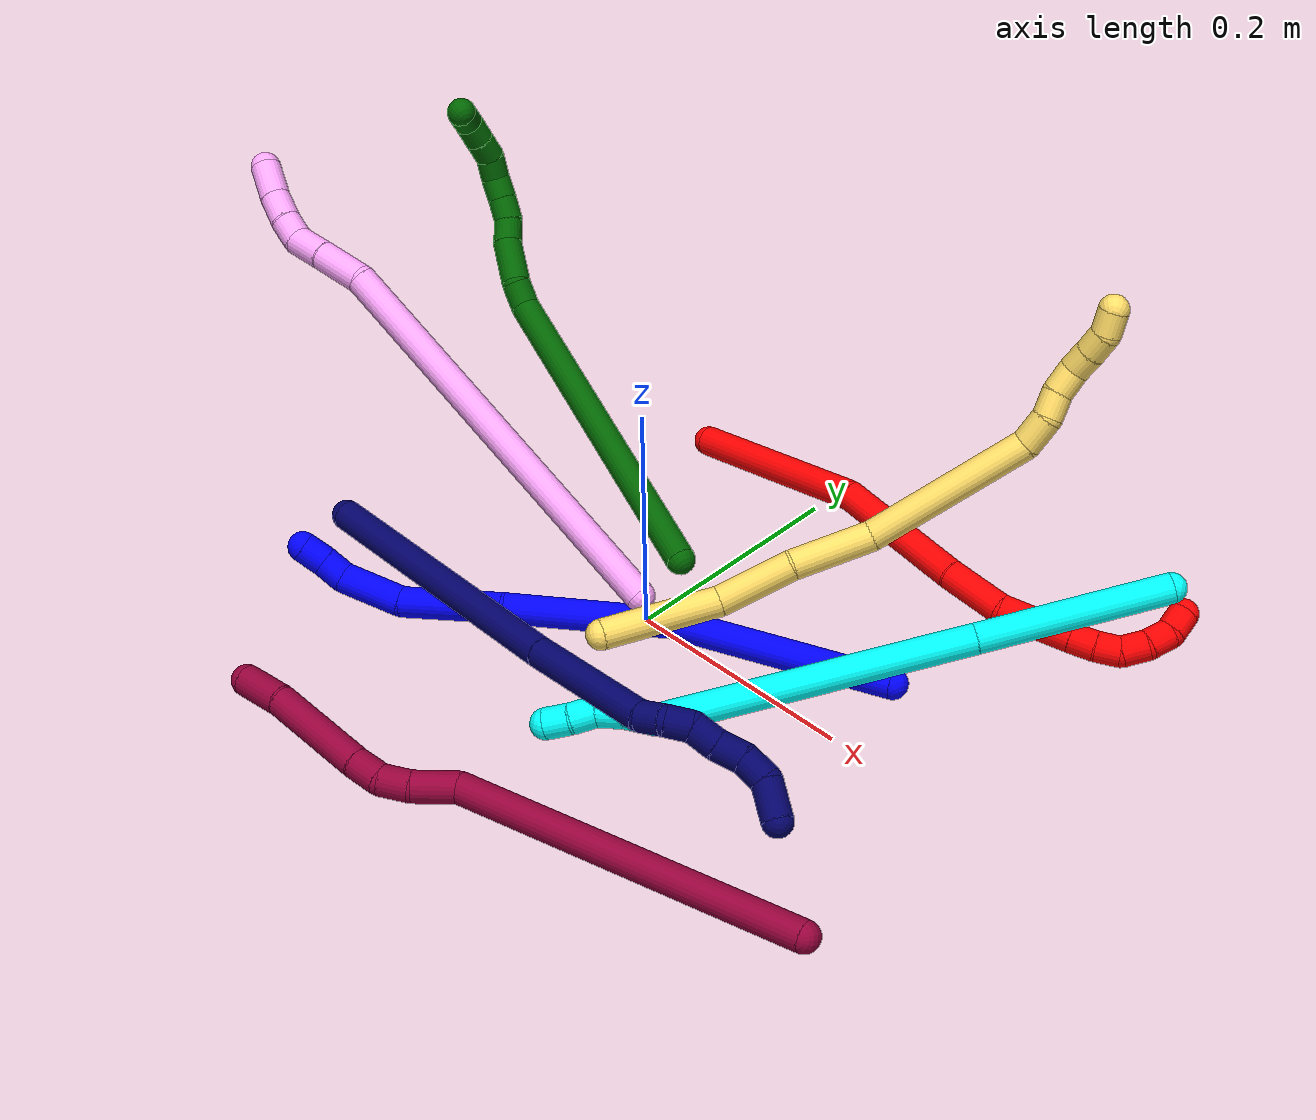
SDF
<sdf version="1.7">
 <world name="default">
  <plugin name="TubeGeneratorPlugin" filename="libtube_generator_plugin.so"/>
  <model name="photoneo_s_sensor">
   <static>1</static>
   <pose>0 0 2 1.57079 1.57079 3.14159</pose>
   <link name="link">
    <inertial><mass>0.1</mass></inertial>
    <sensor name="sensor" type="depth">
     <update_rate>30</update_rate>
     <camera>
      <horizontal_fov>1.22</horizontal_fov>
      <image><width>1920</width><height>1200</height><format>B8G8R8</format></image>
      <clip><near>0.1</near><far>4</far></clip>
      <depth_camera><output>points</output></depth_camera>
     </camera>
     <plugin name="camera_plugin" filename="libgazebo_ros_depth_camera.so">
      <baseline>0.2</baseline>
      <alwaysOn>1</alwaysOn>
      <updateRate>0.0</updateRate>
      <cameraName>camera_ir</cameraName>
      <imageTopicName>/camera/color/image_raw</imageTopicName>
      <cameraInfoTopicName>/camera/color/camera_info</cameraInfoTopicName>
      <depthImageTopicName>/camera/depth/image_raw</depthImageTopicName>
      <depthImageCameraInfoTopicName>/camera/depth/camera_info</depthImageCameraInfoTopicName>
      <pointCloudTopicName>/camera/depth/points</pointCloudTopicName>
      <frameName>fr_optical</frameName>
      <pointCloudCutoff>0.1</pointCloudCutoff>
      <pointCloudCutoffMax>2.0</pointCloudCutoffMax>
      <distortionK1>0</distortionK1>
      <distortionK2>0</distortionK2>
      <distortionK3>0</distortionK3>
      <distortionT1>0</distortionT1>
      <distortionT2>0</distortionT2>
      <CxPrime>0</CxPrime>
      <Cx>0</Cx>
      <Cy>0</Cy>
      <focalLength>0</focalLength>
      <hackBaseline>0</hackBaseline>
     </plugin>
    </sensor>
   </link>
  </model>
  <gravity>0 0 -9.8</gravity>
  <magnetic_field>6e-06 2.3e-05 -4.2e-05</magnetic_field>
  <atmosphere type="adiabatic"/>
  <physics name="default_physics" default="0" type="ode">
   <max_step_size>0.003</max_step_size>
   <real_time_factor>1</real_time_factor>
   <real_time_update_rate>1000</real_time_update_rate>
   <max_contacts>10000</max_contacts>
   <ode>
    <solver>
     <type>quick</type>
     <iters>100</iters>
     <sor>1.3</sor>
     <use_dynamic_moi_rescaling>0</use_dynamic_moi_rescaling>
    </solver>
    <constraints>
     <contact_max_correcting_vel>0</contact_max_correcting_vel>
     <contact_surface_layer>0.001</contact_surface_layer>
     <cfm>0</cfm>
     <erp>0.2</erp>
    </constraints>
   </ode>
  </physics>
  <scene><ambient>0.4 0.4 0.4 1</ambient><background>0.7 0.7 0.7 1</background><shadows>0</shadows></scene>
  <audio><device>default</device></audio>
  <spherical_coordinates>
   <surface_model>EARTH_WGS84</surface_model>
   <latitude_deg>0</latitude_deg>
   <longitude_deg>0</longitude_deg>
   <elevation>0</elevation>
   <heading_deg>0</heading_deg>
  </spherical_coordinates>
  <model name="bin">
   <static>1</static>
   <link name="bottom">
    <collision name="collision-bottom">
     <pose>0 0 -0.01 0 -0 0</pose>
     <geometry><box><size>0.8 0.6 0.02</size></box></geometry>
     <surface>
      <friction><ode><mu>100</mu><mu2>100</mu2></ode></friction>
      <contact><collide_bitmask>65535</collide_bitmask></contact>
     </surface>
    </collision>
   </link>
   <link name="west_wall">
    <collision name="collision-west_wall">
     <pose>-0.41 0 0.1 0 -0 0</pose>
     <geometry><box><size>0.02 0.6 0.2</size></box></geometry>
     <surface>
      <friction><ode><mu>100</mu><mu2>100</mu2></ode></friction>
      <contact><collide_bitmask>65535</collide_bitmask></contact>
     </surface>
    </collision>
   </link>
   <link name="east_wall">
    <collision name="collision-east_wall">
     <pose>0.41 0 0.1 0 -0 0</pose>
     <geometry><box><size>0.02 0.6 0.2</size></box></geometry>
     <surface>
      <friction><ode><mu>100</mu><mu2>100</mu2></ode></friction>
      <contact><collide_bitmask>65535</collide_bitmask></contact>
     </surface>
    </collision>
   </link>
   <link name="south_wall">
    <collision name="collision-south_wall">
     <pose>0 -0.31 0.1 0 -0 0</pose>
     <geometry><box><size>0.8 0.02 0.2</size></box></geometry>
     <surface>
      <friction><ode><mu>100</mu><mu2>100</mu2></ode></friction>
      <contact><collide_bitmask>65535</collide_bitmask></contact>
     </surface>
    </collision>
   </link>
   <link name="north_wall">
    <collision name="collision-north_wall">
     <pose>0 0.31 0.1 0 -0 0</pose>
     <geometry><box><size>0.8 0.02 0.2</size></box></geometry>
     <surface>
      <friction><ode><mu>100</mu><mu2>100</mu2></ode></friction>
      <contact><collide_bitmask>65535</collide_bitmask></contact>
     </surface>
    </collision>
   </link>
  </model>
  <model name="1">
   <static>0</static>
   <link name="1">
    <collision name="collision-cylinder-e_1_1_4">
     <pose>-0.064856 -0.023432 0.061577 0.363607 -0.77753 -0.150317</pose>
     <geometry><cylinder><radius>0.0125</radius><length>0.184902</length></cylinder></geometry>
     <surface>
      <friction><ode><mu>1.16</mu><mu2>1.16</mu2><slip1>0</slip1><slip2>0</slip2></ode></friction>
      <contact><ode><kp>1e+06</kp><kd>1</kd><max_vel>0</max_vel><min_depth>0.001</min_depth></ode></contact>
     </surface>
    </collision>
    <visual name="visual-cylinder-e_1_1_4">
     <pose>-0.064856 -0.023432 0.061577 0.363607 -0.77753 -0.150317</pose>
     <geometry><cylinder><radius>0.0125</radius><length>0.184902</length></cylinder></geometry>
     <material><ambient>0 0 1 1</ambient></material>
    </visual>
    <collision name="collision-cylinder-e_2_4_5">
     <pose>-0.176876 -0.083704 0.154772 0.861557 -0.770938 -0.368718</pose>
     <geometry><cylinder><radius>0.0125</radius><length>0.135369</length></cylinder></geometry>
     <surface>
      <friction><ode><mu>1.16</mu><mu2>1.16</mu2><slip1>0</slip1><slip2>0</slip2></ode></friction>
      <contact><ode><kp>1e+06</kp><kd>1</kd><max_vel>0</max_vel><min_depth>0.001</min_depth></ode></contact>
     </surface>
    </collision>
    <visual name="visual-cylinder-e_2_4_5">
     <pose>-0.176876 -0.083704 0.154772 0.861557 -0.770938 -0.368718</pose>
     <geometry><cylinder><radius>0.0125</radius><length>0.135369</length></cylinder></geometry>
     <material><ambient>0 0 1 1</ambient></material>
    </visual>
    <collision name="collision-cylinder-e_3_5_6">
     <pose>-0.258236 -0.134458 0.207609 0.580351 -0.932403 -0.298282</pose>
     <geometry><cylinder><radius>0.0125</radius><length>0.085168</length></cylinder></geometry>
     <surface>
      <friction><ode><mu>1.16</mu><mu2>1.16</mu2><slip1>0</slip1><slip2>0</slip2></ode></friction>
      <contact><ode><kp>1e+06</kp><kd>1</kd><max_vel>0</max_vel><min_depth>0.001</min_depth></ode></contact>
     </surface>
    </collision>
    <visual name="visual-cylinder-e_3_5_6">
     <pose>-0.258236 -0.134458 0.207609 0.580351 -0.932403 -0.298282</pose>
     <geometry><cylinder><radius>0.0125</radius><length>0.085168</length></cylinder></geometry>
     <material><ambient>0 0 1 1</ambient></material>
    </visual>
    <collision name="collision-cylinder-e_4_6_7">
     <pose>-0.308448 -0.156646 0.248606 0.396243 -0.641622 -0.13322</pose>
     <geometry><cylinder><radius>0.0125</radius><length>0.053516</length></cylinder></geometry>
     <surface>
      <friction><ode><mu>1.16</mu><mu2>1.16</mu2><slip1>0</slip1><slip2>0</slip2></ode></friction>
      <contact><ode><kp>1e+06</kp><kd>1</kd><max_vel>0</max_vel><min_depth>0.001</min_depth></ode></contact>
     </surface>
    </collision>
    <visual name="visual-cylinder-e_4_6_7">
     <pose>-0.308448 -0.156646 0.248606 0.396243 -0.641622 -0.13322</pose>
     <geometry><cylinder><radius>0.0125</radius><length>0.053516</length></cylinder></geometry>
     <material><ambient>0 0 1 1</ambient></material>
    </visual>
    <collision name="collision-cylinder-e_5_7_8">
     <pose>-0.326814 -0.170002 0.277006 0.532533 -0.230727 -0.063189</pose>
     <geometry><cylinder><radius>0.0125</radius><length>0.020567</length></cylinder></geometry>
     <surface>
      <friction><ode><mu>1.16</mu><mu2>1.16</mu2><slip1>0</slip1><slip2>0</slip2></ode></friction>
      <contact><ode><kp>1e+06</kp><kd>1</kd><max_vel>0</max_vel><min_depth>0.001</min_depth></ode></contact>
     </surface>
    </collision>
    <visual name="visual-cylinder-e_5_7_8">
     <pose>-0.326814 -0.170002 0.277006 0.532533 -0.230727 -0.063189</pose>
     <geometry><cylinder><radius>0.0125</radius><length>0.020567</length></cylinder></geometry>
     <material><ambient>0 0 1 1</ambient></material>
    </visual>
    <collision name="collision-cylinder-e_6_8_2">
     <pose>-0.332005 -0.180864 0.293593 0.62787 -0.280982 -0.091768</pose>
     <geometry><cylinder><radius>0.0125</radius><length>0.020479</length></cylinder></geometry>
     <surface>
      <friction><ode><mu>1.16</mu><mu2>1.16</mu2><slip1>0</slip1><slip2>0</slip2></ode></friction>
      <contact><ode><kp>1e+06</kp><kd>1</kd><max_vel>0</max_vel><min_depth>0.001</min_depth></ode></contact>
     </surface>
    </collision>
    <visual name="visual-cylinder-e_6_8_2">
     <pose>-0.332005 -0.180864 0.293593 0.62787 -0.280982 -0.091768</pose>
     <geometry><cylinder><radius>0.0125</radius><length>0.020479</length></cylinder></geometry>
     <material><ambient>0 0 1 1</ambient></material>
    </visual>
    <collision name="collision-sphere-2">
     <pose>-0.334844 -0.186643 0.301554 0 -0 0</pose>
     <geometry><sphere><radius>0.0125</radius></sphere></geometry>
     <surface>
      <friction><ode><mu>1.16</mu><mu2>1.16</mu2><slip1>0</slip1><slip2>0</slip2></ode></friction>
      <contact><ode><kp>1e+06</kp><kd>1</kd><max_vel>0</max_vel><min_depth>0.001</min_depth></ode></contact>
     </surface>
    </collision>
    <visual name="visual-sphere-2">
     <pose>-0.334844 -0.186643 0.301554 0 -0 0</pose>
     <geometry><sphere><radius>0.0125</radius></sphere></geometry>
     <material><ambient>0 0 1 1</ambient></material>
    </visual>
    <collision name="collision-sphere-4">
     <pose>-0.129713 -0.046864 0.123155 0 -0 0</pose>
     <geometry><sphere><radius>0.0125</radius></sphere></geometry>
     <surface>
      <friction><ode><mu>1.16</mu><mu2>1.16</mu2><slip1>0</slip1><slip2>0</slip2></ode></friction>
      <contact><ode><kp>1e+06</kp><kd>1</kd><max_vel>0</max_vel><min_depth>0.001</min_depth></ode></contact>
     </surface>
    </collision>
    <visual name="visual-sphere-4">
     <pose>-0.129713 -0.046864 0.123155 0 -0 0</pose>
     <geometry><sphere><radius>0.0125</radius></sphere></geometry>
     <material><ambient>0 0 1 1</ambient></material>
    </visual>
    <collision name="collision-sphere-1">
     <geometry><sphere><radius>0.0125</radius></sphere></geometry>
     <surface>
      <friction><ode><mu>1.16</mu><mu2>1.16</mu2><slip1>0</slip1><slip2>0</slip2></ode></friction>
      <contact><ode><kp>1e+06</kp><kd>1</kd><max_vel>0</max_vel><min_depth>0.001</min_depth></ode></contact>
     </surface>
    </collision>
    <visual name="visual-sphere-1">
     <geometry><sphere><radius>0.0125</radius></sphere></geometry>
     <material><ambient>0 0 1 1</ambient></material>
    </visual>
    <collision name="collision-sphere-8">
     <pose>-0.329166 -0.175085 0.285631 0 -0 0</pose>
     <geometry><sphere><radius>0.0125</radius></sphere></geometry>
     <surface>
      <friction><ode><mu>1.16</mu><mu2>1.16</mu2><slip1>0</slip1><slip2>0</slip2></ode></friction>
      <contact><ode><kp>1e+06</kp><kd>1</kd><max_vel>0</max_vel><min_depth>0.001</min_depth></ode></contact>
     </surface>
    </collision>
    <visual name="visual-sphere-8">
     <pose>-0.329166 -0.175085 0.285631 0 -0 0</pose>
     <geometry><sphere><radius>0.0125</radius></sphere></geometry>
     <material><ambient>0 0 1 1</ambient></material>
    </visual>
    <collision name="collision-sphere-5">
     <pose>-0.224039 -0.120544 0.186388 0 -0 0</pose>
     <geometry><sphere><radius>0.0125</radius></sphere></geometry>
     <surface>
      <friction><ode><mu>1.16</mu><mu2>1.16</mu2><slip1>0</slip1><slip2>0</slip2></ode></friction>
      <contact><ode><kp>1e+06</kp><kd>1</kd><max_vel>0</max_vel><min_depth>0.001</min_depth></ode></contact>
     </surface>
    </collision>
    <visual name="visual-sphere-5">
     <pose>-0.224039 -0.120544 0.186388 0 -0 0</pose>
     <geometry><sphere><radius>0.0125</radius></sphere></geometry>
     <material><ambient>0 0 1 1</ambient></material>
    </visual>
    <collision name="collision-sphere-6">
     <pose>-0.292433 -0.148373 0.228831 0 -0 0</pose>
     <geometry><sphere><radius>0.0125</radius></sphere></geometry>
     <surface>
      <friction><ode><mu>1.16</mu><mu2>1.16</mu2><slip1>0</slip1><slip2>0</slip2></ode></friction>
      <contact><ode><kp>1e+06</kp><kd>1</kd><max_vel>0</max_vel><min_depth>0.001</min_depth></ode></contact>
     </surface>
    </collision>
    <visual name="visual-sphere-6">
     <pose>-0.292433 -0.148373 0.228831 0 -0 0</pose>
     <geometry><sphere><radius>0.0125</radius></sphere></geometry>
     <material><ambient>0 0 1 1</ambient></material>
    </visual>
    <collision name="collision-sphere-7">
     <pose>-0.324462 -0.16492 0.268382 0 -0 0</pose>
     <geometry><sphere><radius>0.0125</radius></sphere></geometry>
     <surface>
      <friction><ode><mu>1.16</mu><mu2>1.16</mu2><slip1>0</slip1><slip2>0</slip2></ode></friction>
      <contact><ode><kp>1e+06</kp><kd>1</kd><max_vel>0</max_vel><min_depth>0.001</min_depth></ode></contact>
     </surface>
    </collision>
    <visual name="visual-sphere-7">
     <pose>-0.324462 -0.16492 0.268382 0 -0 0</pose>
     <geometry><sphere><radius>0.0125</radius></sphere></geometry>
     <material><ambient>0 0 1 1</ambient></material>
    </visual>
    <inertial>
     <pose>-0.175913 -0.085397 0.150065 0 -0 0</pose>
     <mass>0.5</mass>
     <inertia>
      <ixx>0.000415</ixx>
      <ixy>0</ixy>
      <ixz>0</ixz>
      <iyy>0.000612</iyy>
      <iyz>0</iyz>
      <izz>0.000874</izz>
     </inertia>
    </inertial>
   </link>
   <pose>0.200845 0.068662 0.012153 -0.870307 -0.727832 0.724106</pose>
  </model>
  <model name="2">
   <static>0</static>
   <link name="2">
    <collision name="collision-cylinder-e_1_1_4">
     <pose>0.023934 0.019014 0.078383 -0.237981 0.288469 -0.034726</pose>
     <geometry><cylinder><radius>0.0125</radius><length>0.168264</length></cylinder></geometry>
     <surface>
      <friction><ode><mu>1.16</mu><mu2>1.16</mu2><slip1>0</slip1><slip2>0</slip2></ode></friction>
      <contact><ode><kp>1e+06</kp><kd>1</kd><max_vel>0</max_vel><min_depth>0.001</min_depth></ode></contact>
     </surface>
    </collision>
    <visual name="visual-cylinder-e_1_1_4">
     <pose>0.023934 0.019014 0.078383 -0.237981 0.288469 -0.034726</pose>
     <geometry><cylinder><radius>0.0125</radius><length>0.168264</length></cylinder></geometry>
     <material><ambient>1 0 0 1</ambient></material>
    </visual>
    <collision name="collision-cylinder-e_2_4_5">
     <pose>0.052399 0.039724 0.215558 -0.028844 0.076878 -0.001109</pose>
     <geometry><cylinder><radius>0.0125</radius><length>0.117983</length></cylinder></geometry>
     <surface>
      <friction><ode><mu>1.16</mu><mu2>1.16</mu2><slip1>0</slip1><slip2>0</slip2></ode></friction>
      <contact><ode><kp>1e+06</kp><kd>1</kd><max_vel>0</max_vel><min_depth>0.001</min_depth></ode></contact>
     </surface>
    </collision>
    <visual name="visual-cylinder-e_2_4_5">
     <pose>0.052399 0.039724 0.215558 -0.028844 0.076878 -0.001109</pose>
     <geometry><cylinder><radius>0.0125</radius><length>0.117983</length></cylinder></geometry>
     <material><ambient>1 0 0 1</ambient></material>
    </visual>
    <collision name="collision-cylinder-e_3_5_6">
     <pose>0.060477 0.039354 0.299524 0.081882 0.139534 0.005725</pose>
     <geometry><cylinder><radius>0.0125</radius><length>0.051012</length></cylinder></geometry>
     <surface>
      <friction><ode><mu>1.16</mu><mu2>1.16</mu2><slip1>0</slip1><slip2>0</slip2></ode></friction>
      <contact><ode><kp>1e+06</kp><kd>1</kd><max_vel>0</max_vel><min_depth>0.001</min_depth></ode></contact>
     </surface>
    </collision>
    <visual name="visual-cylinder-e_3_5_6">
     <pose>0.060477 0.039354 0.299524 0.081882 0.139534 0.005725</pose>
     <geometry><cylinder><radius>0.0125</radius><length>0.051012</length></cylinder></geometry>
     <material><ambient>1 0 0 1</ambient></material>
    </visual>
    <collision name="collision-cylinder-e_4_6_7">
     <pose>0.070673 0.032499 0.340397 0.296138 0.384833 0.058105</pose>
     <geometry><cylinder><radius>0.0125</radius><length>0.035418</length></cylinder></geometry>
     <surface>
      <friction><ode><mu>1.16</mu><mu2>1.16</mu2><slip1>0</slip1><slip2>0</slip2></ode></friction>
      <contact><ode><kp>1e+06</kp><kd>1</kd><max_vel>0</max_vel><min_depth>0.001</min_depth></ode></contact>
     </surface>
    </collision>
    <visual name="visual-cylinder-e_4_6_7">
     <pose>0.070673 0.032499 0.340397 0.296138 0.384833 0.058105</pose>
     <geometry><cylinder><radius>0.0125</radius><length>0.035418</length></cylinder></geometry>
     <material><ambient>1 0 0 1</ambient></material>
    </visual>
    <collision name="collision-cylinder-e_5_7_8">
     <pose>0.081807 0.024534 0.366798 0.288349 0.38212 0.056147</pose>
     <geometry><cylinder><radius>0.0125</radius><length>0.024059</length></cylinder></geometry>
     <surface>
      <friction><ode><mu>1.16</mu><mu2>1.16</mu2><slip1>0</slip1><slip2>0</slip2></ode></friction>
      <contact><ode><kp>1e+06</kp><kd>1</kd><max_vel>0</max_vel><min_depth>0.001</min_depth></ode></contact>
     </surface>
    </collision>
    <visual name="visual-cylinder-e_5_7_8">
     <pose>0.081807 0.024534 0.366798 0.288349 0.38212 0.056147</pose>
     <geometry><cylinder><radius>0.0125</radius><length>0.024059</length></cylinder></geometry>
     <material><ambient>1 0 0 1</ambient></material>
    </visual>
    <collision name="collision-cylinder-e_6_8_9">
     <pose>0.090514 0.018714 0.386509 0.285717 0.422462 0.061667</pose>
     <geometry><cylinder><radius>0.0125</radius><length>0.020591</length></cylinder></geometry>
     <surface>
      <friction><ode><mu>1.16</mu><mu2>1.16</mu2><slip1>0</slip1><slip2>0</slip2></ode></friction>
      <contact><ode><kp>1e+06</kp><kd>1</kd><max_vel>0</max_vel><min_depth>0.001</min_depth></ode></contact>
     </surface>
    </collision>
    <visual name="visual-cylinder-e_6_8_9">
     <pose>0.090514 0.018714 0.386509 0.285717 0.422462 0.061667</pose>
     <geometry><cylinder><radius>0.0125</radius><length>0.020591</length></cylinder></geometry>
     <material><ambient>1 0 0 1</ambient></material>
    </visual>
    <collision name="collision-cylinder-e_7_9_10">
     <pose>0.100094 0.013184 0.403614 0.342136 0.557629 0.09883</pose>
     <geometry><cylinder><radius>0.0125</radius><length>0.020255</length></cylinder></geometry>
     <surface>
      <friction><ode><mu>1.16</mu><mu2>1.16</mu2><slip1>0</slip1><slip2>0</slip2></ode></friction>
      <contact><ode><kp>1e+06</kp><kd>1</kd><max_vel>0</max_vel><min_depth>0.001</min_depth></ode></contact>
     </surface>
    </collision>
    <visual name="visual-cylinder-e_7_9_10">
     <pose>0.100094 0.013184 0.403614 0.342136 0.557629 0.09883</pose>
     <geometry><cylinder><radius>0.0125</radius><length>0.020255</length></cylinder></geometry>
     <material><ambient>1 0 0 1</ambient></material>
    </visual>
    <collision name="collision-cylinder-e_8_10_11">
     <pose>0.114813 0.007989 0.416736 0.431118 1.03688 0.248543</pose>
     <geometry><cylinder><radius>0.0125</radius><length>0.021746</length></cylinder></geometry>
     <surface>
      <friction><ode><mu>1.16</mu><mu2>1.16</mu2><slip1>0</slip1><slip2>0</slip2></ode></friction>
      <contact><ode><kp>1e+06</kp><kd>1</kd><max_vel>0</max_vel><min_depth>0.001</min_depth></ode></contact>
     </surface>
    </collision>
    <visual name="visual-cylinder-e_8_10_11">
     <pose>0.114813 0.007989 0.416736 0.431118 1.03688 0.248543</pose>
     <geometry><cylinder><radius>0.0125</radius><length>0.021746</length></cylinder></geometry>
     <material><ambient>1 0 0 1</ambient></material>
    </visual>
    <collision name="collision-cylinder-e_9_11_12">
     <pose>0.13361 0.002559 0.423691 1.01683 1.20033 0.728723</pose>
     <geometry><cylinder><radius>0.0125</radius><length>0.020249</length></cylinder></geometry>
     <surface>
      <friction><ode><mu>1.16</mu><mu2>1.16</mu2><slip1>0</slip1><slip2>0</slip2></ode></friction>
      <contact><ode><kp>1e+06</kp><kd>1</kd><max_vel>0</max_vel><min_depth>0.001</min_depth></ode></contact>
     </surface>
    </collision>
    <visual name="visual-cylinder-e_9_11_12">
     <pose>0.13361 0.002559 0.423691 1.01683 1.20033 0.728723</pose>
     <geometry><cylinder><radius>0.0125</radius><length>0.020249</length></cylinder></geometry>
     <material><ambient>1 0 0 1</ambient></material>
    </visual>
    <collision name="collision-cylinder-e_10_12_2">
     <pose>0.152458 -0.003361 0.422817 2.35605 1.17222 2.02583</pose>
     <geometry><cylinder><radius>0.0125</radius><length>0.020423</length></cylinder></geometry>
     <surface>
      <friction><ode><mu>1.16</mu><mu2>1.16</mu2><slip1>0</slip1><slip2>0</slip2></ode></friction>
      <contact><ode><kp>1e+06</kp><kd>1</kd><max_vel>0</max_vel><min_depth>0.001</min_depth></ode></contact>
     </surface>
    </collision>
    <visual name="visual-cylinder-e_10_12_2">
     <pose>0.152458 -0.003361 0.422817 2.35605 1.17222 2.02583</pose>
     <geometry><cylinder><radius>0.0125</radius><length>0.020423</length></cylinder></geometry>
     <material><ambient>1 0 0 1</ambient></material>
    </visual>
    <collision name="collision-sphere-2">
     <pose>0.161869 -0.006164 0.420015 0 -0 0</pose>
     <geometry><sphere><radius>0.0125</radius></sphere></geometry>
     <surface>
      <friction><ode><mu>1.16</mu><mu2>1.16</mu2><slip1>0</slip1><slip2>0</slip2></ode></friction>
      <contact><ode><kp>1e+06</kp><kd>1</kd><max_vel>0</max_vel><min_depth>0.001</min_depth></ode></contact>
     </surface>
    </collision>
    <visual name="visual-sphere-2">
     <pose>0.161869 -0.006164 0.420015 0 -0 0</pose>
     <geometry><sphere><radius>0.0125</radius></sphere></geometry>
     <material><ambient>1 0 0 1</ambient></material>
    </visual>
    <collision name="collision-sphere-12">
     <pose>0.143048 -0.000558 0.425619 0 -0 0</pose>
     <geometry><sphere><radius>0.0125</radius></sphere></geometry>
     <surface>
      <friction><ode><mu>1.16</mu><mu2>1.16</mu2><slip1>0</slip1><slip2>0</slip2></ode></friction>
      <contact><ode><kp>1e+06</kp><kd>1</kd><max_vel>0</max_vel><min_depth>0.001</min_depth></ode></contact>
     </surface>
    </collision>
    <visual name="visual-sphere-12">
     <pose>0.143048 -0.000558 0.425619 0 -0 0</pose>
     <geometry><sphere><radius>0.0125</radius></sphere></geometry>
     <material><ambient>1 0 0 1</ambient></material>
    </visual>
    <collision name="collision-sphere-11">
     <pose>0.124172 0.005676 0.421763 0 -0 0</pose>
     <geometry><sphere><radius>0.0125</radius></sphere></geometry>
     <surface>
      <friction><ode><mu>1.16</mu><mu2>1.16</mu2><slip1>0</slip1><slip2>0</slip2></ode></friction>
      <contact><ode><kp>1e+06</kp><kd>1</kd><max_vel>0</max_vel><min_depth>0.001</min_depth></ode></contact>
     </surface>
    </collision>
    <visual name="visual-sphere-11">
     <pose>0.124172 0.005676 0.421763 0 -0 0</pose>
     <geometry><sphere><radius>0.0125</radius></sphere></geometry>
     <material><ambient>1 0 0 1</ambient></material>
    </visual>
    <collision name="collision-sphere-10">
     <pose>0.105453 0.010301 0.411709 0 -0 0</pose>
     <geometry><sphere><radius>0.0125</radius></sphere></geometry>
     <surface>
      <friction><ode><mu>1.16</mu><mu2>1.16</mu2><slip1>0</slip1><slip2>0</slip2></ode></friction>
      <contact><ode><kp>1e+06</kp><kd>1</kd><max_vel>0</max_vel><min_depth>0.001</min_depth></ode></contact>
     </surface>
    </collision>
    <visual name="visual-sphere-10">
     <pose>0.105453 0.010301 0.411709 0 -0 0</pose>
     <geometry><sphere><radius>0.0125</radius></sphere></geometry>
     <material><ambient>1 0 0 1</ambient></material>
    </visual>
    <collision name="collision-sphere-9">
     <pose>0.094735 0.016067 0.395519 0 -0 0</pose>
     <geometry><sphere><radius>0.0125</radius></sphere></geometry>
     <surface>
      <friction><ode><mu>1.16</mu><mu2>1.16</mu2><slip1>0</slip1><slip2>0</slip2></ode></friction>
      <contact><ode><kp>1e+06</kp><kd>1</kd><max_vel>0</max_vel><min_depth>0.001</min_depth></ode></contact>
     </surface>
    </collision>
    <visual name="visual-sphere-9">
     <pose>0.094735 0.016067 0.395519 0 -0 0</pose>
     <geometry><sphere><radius>0.0125</radius></sphere></geometry>
     <material><ambient>1 0 0 1</ambient></material>
    </visual>
    <collision name="collision-sphere-4">
     <pose>0.047869 0.038028 0.156765 0 -0 0</pose>
     <geometry><sphere><radius>0.0125</radius></sphere></geometry>
     <surface>
      <friction><ode><mu>1.16</mu><mu2>1.16</mu2><slip1>0</slip1><slip2>0</slip2></ode></friction>
      <contact><ode><kp>1e+06</kp><kd>1</kd><max_vel>0</max_vel><min_depth>0.001</min_depth></ode></contact>
     </surface>
    </collision>
    <visual name="visual-sphere-4">
     <pose>0.047869 0.038028 0.156765 0 -0 0</pose>
     <geometry><sphere><radius>0.0125</radius></sphere></geometry>
     <material><ambient>1 0 0 1</ambient></material>
    </visual>
    <collision name="collision-sphere-1">
     <geometry><sphere><radius>0.0125</radius></sphere></geometry>
     <surface>
      <friction><ode><mu>1.16</mu><mu2>1.16</mu2><slip1>0</slip1><slip2>0</slip2></ode></friction>
      <contact><ode><kp>1e+06</kp><kd>1</kd><max_vel>0</max_vel><min_depth>0.001</min_depth></ode></contact>
     </surface>
    </collision>
    <visual name="visual-sphere-1">
     <geometry><sphere><radius>0.0125</radius></sphere></geometry>
     <material><ambient>1 0 0 1</ambient></material>
    </visual>
    <collision name="collision-sphere-8">
     <pose>0.086292 0.02136 0.377499 0 -0 0</pose>
     <geometry><sphere><radius>0.0125</radius></sphere></geometry>
     <surface>
      <friction><ode><mu>1.16</mu><mu2>1.16</mu2><slip1>0</slip1><slip2>0</slip2></ode></friction>
      <contact><ode><kp>1e+06</kp><kd>1</kd><max_vel>0</max_vel><min_depth>0.001</min_depth></ode></contact>
     </surface>
    </collision>
    <visual name="visual-sphere-8">
     <pose>0.086292 0.02136 0.377499 0 -0 0</pose>
     <geometry><sphere><radius>0.0125</radius></sphere></geometry>
     <material><ambient>1 0 0 1</ambient></material>
    </visual>
    <collision name="collision-sphere-5">
     <pose>0.05693 0.04142 0.274351 0 -0 0</pose>
     <geometry><sphere><radius>0.0125</radius></sphere></geometry>
     <surface>
      <friction><ode><mu>1.16</mu><mu2>1.16</mu2><slip1>0</slip1><slip2>0</slip2></ode></friction>
      <contact><ode><kp>1e+06</kp><kd>1</kd><max_vel>0</max_vel><min_depth>0.001</min_depth></ode></contact>
     </surface>
    </collision>
    <visual name="visual-sphere-5">
     <pose>0.05693 0.04142 0.274351 0 -0 0</pose>
     <geometry><sphere><radius>0.0125</radius></sphere></geometry>
     <material><ambient>1 0 0 1</ambient></material>
    </visual>
    <collision name="collision-sphere-6">
     <pose>0.064025 0.037289 0.324698 0 -0 0</pose>
     <geometry><sphere><radius>0.0125</radius></sphere></geometry>
     <surface>
      <friction><ode><mu>1.16</mu><mu2>1.16</mu2><slip1>0</slip1><slip2>0</slip2></ode></friction>
      <contact><ode><kp>1e+06</kp><kd>1</kd><max_vel>0</max_vel><min_depth>0.001</min_depth></ode></contact>
     </surface>
    </collision>
    <visual name="visual-sphere-6">
     <pose>0.064025 0.037289 0.324698 0 -0 0</pose>
     <geometry><sphere><radius>0.0125</radius></sphere></geometry>
     <material><ambient>1 0 0 1</ambient></material>
    </visual>
    <collision name="collision-sphere-7">
     <pose>0.077321 0.027708 0.356097 0 -0 0</pose>
     <geometry><sphere><radius>0.0125</radius></sphere></geometry>
     <surface>
      <friction><ode><mu>1.16</mu><mu2>1.16</mu2><slip1>0</slip1><slip2>0</slip2></ode></friction>
      <contact><ode><kp>1e+06</kp><kd>1</kd><max_vel>0</max_vel><min_depth>0.001</min_depth></ode></contact>
     </surface>
    </collision>
    <visual name="visual-sphere-7">
     <pose>0.077321 0.027708 0.356097 0 -0 0</pose>
     <geometry><sphere><radius>0.0125</radius></sphere></geometry>
     <material><ambient>1 0 0 1</ambient></material>
    </visual>
    <inertial>
     <pose>0.059946 0.024888 0.234384 0 -0 0</pose>
     <mass>0.5</mass>
     <inertia>
      <ixx>0.000552</ixx>
      <ixy>0</ixy>
      <ixz>0</ixz>
      <iyy>0.000549</iyy>
      <iyz>0</iyz>
      <izz>-0.000193</izz>
     </inertia>
    </inertial>
   </link>
   <pose>-0.120292 0.195516 0.01141 1.77078 -0.597067 1.32875</pose>
  </model>
  <model name="3">
   <static>0</static>
   <link name="3">
    <collision name="collision-cylinder-e_1_1_4">
     <pose>-0.026676 -0.02267 -0.071216 2.8334 -0.342832 -1.67901</pose>
     <geometry><cylinder><radius>0.0125</radius><length>0.158711</length></cylinder></geometry>
     <surface>
      <friction><ode><mu>1.16</mu><mu2>1.16</mu2><slip1>0</slip1><slip2>0</slip2></ode></friction>
      <contact><ode><kp>1e+06</kp><kd>1</kd><max_vel>0</max_vel><min_depth>0.001</min_depth></ode></contact>
     </surface>
    </collision>
    <visual name="visual-cylinder-e_1_1_4">
     <pose>-0.026676 -0.02267 -0.071216 2.8334 -0.342832 -1.67901</pose>
     <geometry><cylinder><radius>0.0125</radius><length>0.158711</length></cylinder></geometry>
     <material><ambient>0.003922 1 0.996078 1</ambient></material>
    </visual>
    <collision name="collision-cylinder-e_2_4_5">
     <pose>-0.099952 -0.078446 -0.255698 2.85723 -0.376103 -1.85177</pose>
     <geometry><cylinder><radius>0.0125</radius><length>0.253746</length></cylinder></geometry>
     <surface>
      <friction><ode><mu>1.16</mu><mu2>1.16</mu2><slip1>0</slip1><slip2>0</slip2></ode></friction>
      <contact><ode><kp>1e+06</kp><kd>1</kd><max_vel>0</max_vel><min_depth>0.001</min_depth></ode></contact>
     </surface>
    </collision>
    <visual name="visual-cylinder-e_2_4_5">
     <pose>-0.099952 -0.078446 -0.255698 2.85723 -0.376103 -1.85177</pose>
     <geometry><cylinder><radius>0.0125</radius><length>0.253746</length></cylinder></geometry>
     <material><ambient>0.003922 1 0.996078 1</ambient></material>
    </visual>
    <collision name="collision-cylinder-e_3_5_6">
     <pose>-0.150596 -0.108515 -0.381016 -2.89473 -0.314566 1.81393</pose>
     <geometry><cylinder><radius>0.0125</radius><length>0.026141</length></cylinder></geometry>
     <surface>
      <friction><ode><mu>1.16</mu><mu2>1.16</mu2><slip1>0</slip1><slip2>0</slip2></ode></friction>
      <contact><ode><kp>1e+06</kp><kd>1</kd><max_vel>0</max_vel><min_depth>0.001</min_depth></ode></contact>
     </surface>
    </collision>
    <visual name="visual-cylinder-e_3_5_6">
     <pose>-0.150596 -0.108515 -0.381016 -2.89473 -0.314566 1.81393</pose>
     <geometry><cylinder><radius>0.0125</radius><length>0.026141</length></cylinder></geometry>
     <material><ambient>0.003922 1 0.996078 1</ambient></material>
    </visual>
    <collision name="collision-cylinder-e_4_6_7">
     <pose>-0.155226 -0.106755 -0.403553 3.02032 -0.055401 -0.856309</pose>
     <geometry><cylinder><radius>0.0125</radius><length>0.021156</length></cylinder></geometry>
     <surface>
      <friction><ode><mu>1.16</mu><mu2>1.16</mu2><slip1>0</slip1><slip2>0</slip2></ode></friction>
      <contact><ode><kp>1e+06</kp><kd>1</kd><max_vel>0</max_vel><min_depth>0.001</min_depth></ode></contact>
     </surface>
    </collision>
    <visual name="visual-cylinder-e_4_6_7">
     <pose>-0.155226 -0.106755 -0.403553 3.02032 -0.055401 -0.856309</pose>
     <geometry><cylinder><radius>0.0125</radius><length>0.021156</length></cylinder></geometry>
     <material><ambient>0.003922 1 0.996078 1</ambient></material>
    </visual>
    <collision name="collision-cylinder-e_5_7_8">
     <pose>-0.158164 -0.111864 -0.422989 2.73721 -0.237031 -1.05247</pose>
     <geometry><cylinder><radius>0.0125</radius><length>0.020035</length></cylinder></geometry>
     <surface>
      <friction><ode><mu>1.16</mu><mu2>1.16</mu2><slip1>0</slip1><slip2>0</slip2></ode></friction>
      <contact><ode><kp>1e+06</kp><kd>1</kd><max_vel>0</max_vel><min_depth>0.001</min_depth></ode></contact>
     </surface>
    </collision>
    <visual name="visual-cylinder-e_5_7_8">
     <pose>-0.158164 -0.111864 -0.422989 2.73721 -0.237031 -1.05247</pose>
     <geometry><cylinder><radius>0.0125</radius><length>0.020035</length></cylinder></geometry>
     <material><ambient>0.003922 1 0.996078 1</ambient></material>
    </visual>
    <collision name="collision-cylinder-e_6_8_2">
     <pose>-0.161046 -0.119484 -0.441295 2.7568 -0.052491 -0.267899</pose>
     <geometry><cylinder><radius>0.0125</radius><length>0.020212</length></cylinder></geometry>
     <surface>
      <friction><ode><mu>1.16</mu><mu2>1.16</mu2><slip1>0</slip1><slip2>0</slip2></ode></friction>
      <contact><ode><kp>1e+06</kp><kd>1</kd><max_vel>0</max_vel><min_depth>0.001</min_depth></ode></contact>
     </surface>
    </collision>
    <visual name="visual-cylinder-e_6_8_2">
     <pose>-0.161046 -0.119484 -0.441295 2.7568 -0.052491 -0.267899</pose>
     <geometry><cylinder><radius>0.0125</radius><length>0.020212</length></cylinder></geometry>
     <material><ambient>0.003922 1 0.996078 1</ambient></material>
    </visual>
    <collision name="collision-sphere-2">
     <pose>-0.161577 -0.123272 -0.450649 0 -0 0</pose>
     <geometry><sphere><radius>0.0125</radius></sphere></geometry>
     <surface>
      <friction><ode><mu>1.16</mu><mu2>1.16</mu2><slip1>0</slip1><slip2>0</slip2></ode></friction>
      <contact><ode><kp>1e+06</kp><kd>1</kd><max_vel>0</max_vel><min_depth>0.001</min_depth></ode></contact>
     </surface>
    </collision>
    <visual name="visual-sphere-2">
     <pose>-0.161577 -0.123272 -0.450649 0 -0 0</pose>
     <geometry><sphere><radius>0.0125</radius></sphere></geometry>
     <material><ambient>0.003922 1 0.996078 1</ambient></material>
    </visual>
    <collision name="collision-sphere-4">
     <pose>-0.053352 -0.045341 -0.142432 0 -0 0</pose>
     <geometry><sphere><radius>0.0125</radius></sphere></geometry>
     <surface>
      <friction><ode><mu>1.16</mu><mu2>1.16</mu2><slip1>0</slip1><slip2>0</slip2></ode></friction>
      <contact><ode><kp>1e+06</kp><kd>1</kd><max_vel>0</max_vel><min_depth>0.001</min_depth></ode></contact>
     </surface>
    </collision>
    <visual name="visual-sphere-4">
     <pose>-0.053352 -0.045341 -0.142432 0 -0 0</pose>
     <geometry><sphere><radius>0.0125</radius></sphere></geometry>
     <material><ambient>0.003922 1 0.996078 1</ambient></material>
    </visual>
    <collision name="collision-sphere-1">
     <geometry><sphere><radius>0.0125</radius></sphere></geometry>
     <surface>
      <friction><ode><mu>1.16</mu><mu2>1.16</mu2><slip1>0</slip1><slip2>0</slip2></ode></friction>
      <contact><ode><kp>1e+06</kp><kd>1</kd><max_vel>0</max_vel><min_depth>0.001</min_depth></ode></contact>
     </surface>
    </collision>
    <visual name="visual-sphere-1">
     <geometry><sphere><radius>0.0125</radius></sphere></geometry>
     <material><ambient>0.003922 1 0.996078 1</ambient></material>
    </visual>
    <collision name="collision-sphere-8">
     <pose>-0.160516 -0.115695 -0.431941 0 -0 0</pose>
     <geometry><sphere><radius>0.0125</radius></sphere></geometry>
     <surface>
      <friction><ode><mu>1.16</mu><mu2>1.16</mu2><slip1>0</slip1><slip2>0</slip2></ode></friction>
      <contact><ode><kp>1e+06</kp><kd>1</kd><max_vel>0</max_vel><min_depth>0.001</min_depth></ode></contact>
     </surface>
    </collision>
    <visual name="visual-sphere-8">
     <pose>-0.160516 -0.115695 -0.431941 0 -0 0</pose>
     <geometry><sphere><radius>0.0125</radius></sphere></geometry>
     <material><ambient>0.003922 1 0.996078 1</ambient></material>
    </visual>
    <collision name="collision-sphere-5">
     <pose>-0.146552 -0.111552 -0.368964 0 -0 0</pose>
     <geometry><sphere><radius>0.0125</radius></sphere></geometry>
     <surface>
      <friction><ode><mu>1.16</mu><mu2>1.16</mu2><slip1>0</slip1><slip2>0</slip2></ode></friction>
      <contact><ode><kp>1e+06</kp><kd>1</kd><max_vel>0</max_vel><min_depth>0.001</min_depth></ode></contact>
     </surface>
    </collision>
    <visual name="visual-sphere-5">
     <pose>-0.146552 -0.111552 -0.368964 0 -0 0</pose>
     <geometry><sphere><radius>0.0125</radius></sphere></geometry>
     <material><ambient>0.003922 1 0.996078 1</ambient></material>
    </visual>
    <collision name="collision-sphere-6">
     <pose>-0.15464 -0.105478 -0.393068 0 -0 0</pose>
     <geometry><sphere><radius>0.0125</radius></sphere></geometry>
     <surface>
      <friction><ode><mu>1.16</mu><mu2>1.16</mu2><slip1>0</slip1><slip2>0</slip2></ode></friction>
      <contact><ode><kp>1e+06</kp><kd>1</kd><max_vel>0</max_vel><min_depth>0.001</min_depth></ode></contact>
     </surface>
    </collision>
    <visual name="visual-sphere-6">
     <pose>-0.15464 -0.105478 -0.393068 0 -0 0</pose>
     <geometry><sphere><radius>0.0125</radius></sphere></geometry>
     <material><ambient>0.003922 1 0.996078 1</ambient></material>
    </visual>
    <collision name="collision-sphere-7">
     <pose>-0.155812 -0.108033 -0.414037 0 -0 0</pose>
     <geometry><sphere><radius>0.0125</radius></sphere></geometry>
     <surface>
      <friction><ode><mu>1.16</mu><mu2>1.16</mu2><slip1>0</slip1><slip2>0</slip2></ode></friction>
      <contact><ode><kp>1e+06</kp><kd>1</kd><max_vel>0</max_vel><min_depth>0.001</min_depth></ode></contact>
     </surface>
    </collision>
    <visual name="visual-sphere-7">
     <pose>-0.155812 -0.108033 -0.414037 0 -0 0</pose>
     <geometry><sphere><radius>0.0125</radius></sphere></geometry>
     <material><ambient>0.003922 1 0.996078 1</ambient></material>
    </visual>
    <inertial>
     <pose>-0.086481 -0.06651 -0.224153 0 -0 0</pose>
     <mass>0.5</mass>
     <inertia>
      <ixx>-0.001942</ixx>
      <ixy>0</ixy>
      <ixz>0</ixz>
      <iyy>-0.000985</iyy>
      <iyz>0</iyz>
      <izz>0.001039</izz>
     </inertia>
    </inertial>
   </link>
   <pose>0.321296 0.254884 0.066934 1.64162 0.216056 2.16824</pose>
  </model>
  <model name="4">
   <static>0</static>
   <link name="4">
    <collision name="collision-cylinder-e_1_1_4">
     <pose>-0.005192 0.023722 0.173768 -0.135679 -0.029596 0.002011</pose>
     <geometry><cylinder><radius>0.0125</radius><length>0.350912</length></cylinder></geometry>
     <surface>
      <friction><ode><mu>1.16</mu><mu2>1.16</mu2><slip1>0</slip1><slip2>0</slip2></ode></friction>
      <contact><ode><kp>1e+06</kp><kd>1</kd><max_vel>0</max_vel><min_depth>0.001</min_depth></ode></contact>
     </surface>
    </collision>
    <visual name="visual-cylinder-e_1_1_4">
     <pose>-0.005192 0.023722 0.173768 -0.135679 -0.029596 0.002011</pose>
     <geometry><cylinder><radius>0.0125</radius><length>0.350912</length></cylinder></geometry>
     <material><ambient>1 0.65098 0.996078 1</ambient></material>
    </visual>
    <collision name="collision-cylinder-e_2_4_5">
     <pose>-0.018049 0.050058 0.36716 -0.132366 -0.369391 0.024764</pose>
     <geometry><cylinder><radius>0.0125</radius><length>0.042461</length></cylinder></geometry>
     <surface>
      <friction><ode><mu>1.16</mu><mu2>1.16</mu2><slip1>0</slip1><slip2>0</slip2></ode></friction>
      <contact><ode><kp>1e+06</kp><kd>1</kd><max_vel>0</max_vel><min_depth>0.001</min_depth></ode></contact>
     </surface>
    </collision>
    <visual name="visual-cylinder-e_2_4_5">
     <pose>-0.018049 0.050058 0.36716 -0.132366 -0.369391 0.024764</pose>
     <geometry><cylinder><radius>0.0125</radius><length>0.042461</length></cylinder></geometry>
     <material><ambient>1 0.65098 0.996078 1</ambient></material>
    </visual>
    <collision name="collision-cylinder-e_3_5_6">
     <pose>-0.032278 0.055611 0.400812 -0.206588 -0.429464 0.045209</pose>
     <geometry><cylinder><radius>0.0125</radius><length>0.031526</length></cylinder></geometry>
     <surface>
      <friction><ode><mu>1.16</mu><mu2>1.16</mu2><slip1>0</slip1><slip2>0</slip2></ode></friction>
      <contact><ode><kp>1e+06</kp><kd>1</kd><max_vel>0</max_vel><min_depth>0.001</min_depth></ode></contact>
     </surface>
    </collision>
    <visual name="visual-cylinder-e_3_5_6">
     <pose>-0.032278 0.055611 0.400812 -0.206588 -0.429464 0.045209</pose>
     <geometry><cylinder><radius>0.0125</radius><length>0.031526</length></cylinder></geometry>
     <material><ambient>1 0.65098 0.996078 1</ambient></material>
    </visual>
    <collision name="collision-cylinder-e_4_6_7">
     <pose>-0.038403 0.061316 0.424866 -0.269156 0.042152 -0.005708</pose>
     <geometry><cylinder><radius>0.0125</radius><length>0.020822</length></cylinder></geometry>
     <surface>
      <friction><ode><mu>1.16</mu><mu2>1.16</mu2><slip1>0</slip1><slip2>0</slip2></ode></friction>
      <contact><ode><kp>1e+06</kp><kd>1</kd><max_vel>0</max_vel><min_depth>0.001</min_depth></ode></contact>
     </surface>
    </collision>
    <visual name="visual-cylinder-e_4_6_7">
     <pose>-0.038403 0.061316 0.424866 -0.269156 0.042152 -0.005708</pose>
     <geometry><cylinder><radius>0.0125</radius><length>0.020822</length></cylinder></geometry>
     <material><ambient>1 0.65098 0.996078 1</ambient></material>
    </visual>
    <collision name="collision-cylinder-e_5_7_8">
     <pose>-0.037383 0.06902 0.445756 -0.426618 0.048696 -0.01055</pose>
     <geometry><cylinder><radius>0.0125</radius><length>0.023893</length></cylinder></geometry>
     <surface>
      <friction><ode><mu>1.16</mu><mu2>1.16</mu2><slip1>0</slip1><slip2>0</slip2></ode></friction>
      <contact><ode><kp>1e+06</kp><kd>1</kd><max_vel>0</max_vel><min_depth>0.001</min_depth></ode></contact>
     </surface>
    </collision>
    <visual name="visual-cylinder-e_5_7_8">
     <pose>-0.037383 0.06902 0.445756 -0.426618 0.048696 -0.01055</pose>
     <geometry><cylinder><radius>0.0125</radius><length>0.023893</length></cylinder></geometry>
     <material><ambient>1 0.65098 0.996078 1</ambient></material>
    </visual>
    <collision name="collision-cylinder-e_6_8_2">
     <pose>-0.03478 0.081121 0.469864 -0.495822 0.133438 -0.033823</pose>
     <geometry><cylinder><radius>0.0125</radius><length>0.030386</length></cylinder></geometry>
     <surface>
      <friction><ode><mu>1.16</mu><mu2>1.16</mu2><slip1>0</slip1><slip2>0</slip2></ode></friction>
      <contact><ode><kp>1e+06</kp><kd>1</kd><max_vel>0</max_vel><min_depth>0.001</min_depth></ode></contact>
     </surface>
    </collision>
    <visual name="visual-cylinder-e_6_8_2">
     <pose>-0.03478 0.081121 0.469864 -0.495822 0.133438 -0.033823</pose>
     <geometry><cylinder><radius>0.0125</radius><length>0.030386</length></cylinder></geometry>
     <material><ambient>1 0.65098 0.996078 1</ambient></material>
    </visual>
    <collision name="collision-sphere-2">
     <pose>-0.032758 0.088285 0.483108 0 -0 0</pose>
     <geometry><sphere><radius>0.0125</radius></sphere></geometry>
     <surface>
      <friction><ode><mu>1.16</mu><mu2>1.16</mu2><slip1>0</slip1><slip2>0</slip2></ode></friction>
      <contact><ode><kp>1e+06</kp><kd>1</kd><max_vel>0</max_vel><min_depth>0.001</min_depth></ode></contact>
     </surface>
    </collision>
    <visual name="visual-sphere-2">
     <pose>-0.032758 0.088285 0.483108 0 -0 0</pose>
     <geometry><sphere><radius>0.0125</radius></sphere></geometry>
     <material><ambient>1 0.65098 0.996078 1</ambient></material>
    </visual>
    <collision name="collision-sphere-4">
     <pose>-0.010384 0.047445 0.347535 0 -0 0</pose>
     <geometry><sphere><radius>0.0125</radius></sphere></geometry>
     <surface>
      <friction><ode><mu>1.16</mu><mu2>1.16</mu2><slip1>0</slip1><slip2>0</slip2></ode></friction>
      <contact><ode><kp>1e+06</kp><kd>1</kd><max_vel>0</max_vel><min_depth>0.001</min_depth></ode></contact>
     </surface>
    </collision>
    <visual name="visual-sphere-4">
     <pose>-0.010384 0.047445 0.347535 0 -0 0</pose>
     <geometry><sphere><radius>0.0125</radius></sphere></geometry>
     <material><ambient>1 0.65098 0.996078 1</ambient></material>
    </visual>
    <collision name="collision-sphere-1">
     <geometry><sphere><radius>0.0125</radius></sphere></geometry>
     <surface>
      <friction><ode><mu>1.16</mu><mu2>1.16</mu2><slip1>0</slip1><slip2>0</slip2></ode></friction>
      <contact><ode><kp>1e+06</kp><kd>1</kd><max_vel>0</max_vel><min_depth>0.001</min_depth></ode></contact>
     </surface>
    </collision>
    <visual name="visual-sphere-1">
     <geometry><sphere><radius>0.0125</radius></sphere></geometry>
     <material><ambient>1 0.65098 0.996078 1</ambient></material>
    </visual>
    <collision name="collision-sphere-8">
     <pose>-0.036801 0.073957 0.456619 0 -0 0</pose>
     <geometry><sphere><radius>0.0125</radius></sphere></geometry>
     <surface>
      <friction><ode><mu>1.16</mu><mu2>1.16</mu2><slip1>0</slip1><slip2>0</slip2></ode></friction>
      <contact><ode><kp>1e+06</kp><kd>1</kd><max_vel>0</max_vel><min_depth>0.001</min_depth></ode></contact>
     </surface>
    </collision>
    <visual name="visual-sphere-8">
     <pose>-0.036801 0.073957 0.456619 0 -0 0</pose>
     <geometry><sphere><radius>0.0125</radius></sphere></geometry>
     <material><ambient>1 0.65098 0.996078 1</ambient></material>
    </visual>
    <collision name="collision-sphere-5">
     <pose>-0.025715 0.052671 0.386786 0 -0 0</pose>
     <geometry><sphere><radius>0.0125</radius></sphere></geometry>
     <surface>
      <friction><ode><mu>1.16</mu><mu2>1.16</mu2><slip1>0</slip1><slip2>0</slip2></ode></friction>
      <contact><ode><kp>1e+06</kp><kd>1</kd><max_vel>0</max_vel><min_depth>0.001</min_depth></ode></contact>
     </surface>
    </collision>
    <visual name="visual-sphere-5">
     <pose>-0.025715 0.052671 0.386786 0 -0 0</pose>
     <geometry><sphere><radius>0.0125</radius></sphere></geometry>
     <material><ambient>1 0.65098 0.996078 1</ambient></material>
    </visual>
    <collision name="collision-sphere-6">
     <pose>-0.038841 0.05855 0.414839 0 -0 0</pose>
     <geometry><sphere><radius>0.0125</radius></sphere></geometry>
     <surface>
      <friction><ode><mu>1.16</mu><mu2>1.16</mu2><slip1>0</slip1><slip2>0</slip2></ode></friction>
      <contact><ode><kp>1e+06</kp><kd>1</kd><max_vel>0</max_vel><min_depth>0.001</min_depth></ode></contact>
     </surface>
    </collision>
    <visual name="visual-sphere-6">
     <pose>-0.038841 0.05855 0.414839 0 -0 0</pose>
     <geometry><sphere><radius>0.0125</radius></sphere></geometry>
     <material><ambient>1 0.65098 0.996078 1</ambient></material>
    </visual>
    <collision name="collision-sphere-7">
     <pose>-0.037964 0.064082 0.434894 0 -0 0</pose>
     <geometry><sphere><radius>0.0125</radius></sphere></geometry>
     <surface>
      <friction><ode><mu>1.16</mu><mu2>1.16</mu2><slip1>0</slip1><slip2>0</slip2></ode></friction>
      <contact><ode><kp>1e+06</kp><kd>1</kd><max_vel>0</max_vel><min_depth>0.001</min_depth></ode></contact>
     </surface>
    </collision>
    <visual name="visual-sphere-7">
     <pose>-0.037964 0.064082 0.434894 0 -0 0</pose>
     <geometry><sphere><radius>0.0125</radius></sphere></geometry>
     <material><ambient>1 0.65098 0.996078 1</ambient></material>
    </visual>
    <inertial>
     <pose>-0.012711 0.035188 0.245955 0 -0 0</pose>
     <mass>0.5</mass>
     <inertia>
      <ixx>0.003636</ixx>
      <ixy>0</ixy>
      <ixz>0</ixz>
      <iyy>0.003614</iyy>
      <iyz>0</iyz>
      <izz>-0.000345</izz>
     </inertia>
    </inertial>
   </link>
   <pose>0.007553 -0.014627 0.0378 -0.253186 -1.035 0.456102</pose>
  </model>
  <model name="5">
   <static>0</static>
   <link name="5">
    <collision name="collision-cylinder-e_1_1_4">
     <pose>-0.004871 0.042871 0.023183 -1.07507 -0.099612 0.059409</pose>
     <geometry><cylinder><radius>0.0125</radius><length>0.097962</length></cylinder></geometry>
     <surface>
      <friction><ode><mu>1.16</mu><mu2>1.16</mu2><slip1>0</slip1><slip2>0</slip2></ode></friction>
      <contact><ode><kp>1e+06</kp><kd>1</kd><max_vel>0</max_vel><min_depth>0.001</min_depth></ode></contact>
     </surface>
    </collision>
    <visual name="visual-cylinder-e_1_1_4">
     <pose>-0.004871 0.042871 0.023183 -1.07507 -0.099612 0.059409</pose>
     <geometry><cylinder><radius>0.0125</radius><length>0.097962</length></cylinder></geometry>
     <material><ambient>1 0.858824 0.4 1</ambient></material>
    </visual>
    <collision name="collision-cylinder-e_2_4_5">
     <pose>-0.001833 0.114068 0.059113 -1.14792 0.249313 -0.161686</pose>
     <geometry><cylinder><radius>0.0125</radius><length>0.064106</length></cylinder></geometry>
     <surface>
      <friction><ode><mu>1.16</mu><mu2>1.16</mu2><slip1>0</slip1><slip2>0</slip2></ode></friction>
      <contact><ode><kp>1e+06</kp><kd>1</kd><max_vel>0</max_vel><min_depth>0.001</min_depth></ode></contact>
     </surface>
    </collision>
    <visual name="visual-cylinder-e_2_4_5">
     <pose>-0.001833 0.114068 0.059113 -1.14792 0.249313 -0.161686</pose>
     <geometry><cylinder><radius>0.0125</radius><length>0.064106</length></cylinder></geometry>
     <material><ambient>1 0.858824 0.4 1</ambient></material>
    </visual>
    <collision name="collision-cylinder-e_3_5_6">
     <pose>0.008233 0.172526 0.086319 -1.12341 0.064476 -0.040585</pose>
     <geometry><cylinder><radius>0.0125</radius><length>0.066983</length></cylinder></geometry>
     <surface>
      <friction><ode><mu>1.16</mu><mu2>1.16</mu2><slip1>0</slip1><slip2>0</slip2></ode></friction>
      <contact><ode><kp>1e+06</kp><kd>1</kd><max_vel>0</max_vel><min_depth>0.001</min_depth></ode></contact>
     </surface>
    </collision>
    <visual name="visual-cylinder-e_3_5_6">
     <pose>0.008233 0.172526 0.086319 -1.12341 0.064476 -0.040585</pose>
     <geometry><cylinder><radius>0.0125</radius><length>0.066983</length></cylinder></geometry>
     <material><ambient>1 0.858824 0.4 1</ambient></material>
    </visual>
    <collision name="collision-cylinder-e_4_6_7">
     <pose>0.034263 0.262577 0.128618 -1.13583 0.346712 -0.222534</pose>
     <geometry><cylinder><radius>0.0125</radius><length>0.1405</length></cylinder></geometry>
     <surface>
      <friction><ode><mu>1.16</mu><mu2>1.16</mu2><slip1>0</slip1><slip2>0</slip2></ode></friction>
      <contact><ode><kp>1e+06</kp><kd>1</kd><max_vel>0</max_vel><min_depth>0.001</min_depth></ode></contact>
     </surface>
    </collision>
    <visual name="visual-cylinder-e_4_6_7">
     <pose>0.034263 0.262577 0.128618 -1.13583 0.346712 -0.222534</pose>
     <geometry><cylinder><radius>0.0125</radius><length>0.1405</length></cylinder></geometry>
     <material><ambient>1 0.858824 0.4 1</ambient></material>
    </visual>
    <collision name="collision-cylinder-e_5_7_8">
     <pose>0.067433 0.330923 0.161875 -0.999617 0.74814 -0.422319</pose>
     <geometry><cylinder><radius>0.0125</radius><length>0.027339</length></cylinder></geometry>
     <surface>
      <friction><ode><mu>1.16</mu><mu2>1.16</mu2><slip1>0</slip1><slip2>0</slip2></ode></friction>
      <contact><ode><kp>1e+06</kp><kd>1</kd><max_vel>0</max_vel><min_depth>0.001</min_depth></ode></contact>
     </surface>
    </collision>
    <visual name="visual-cylinder-e_5_7_8">
     <pose>0.067433 0.330923 0.161875 -0.999617 0.74814 -0.422319</pose>
     <geometry><cylinder><radius>0.0125</radius><length>0.027339</length></cylinder></geometry>
     <material><ambient>1 0.858824 0.4 1</ambient></material>
    </visual>
    <collision name="collision-cylinder-e_6_8_9">
     <pose>0.08373 0.343226 0.174202 -0.510979 0.723518 -0.197041</pose>
     <geometry><cylinder><radius>0.0125</radius><length>0.02114</length></cylinder></geometry>
     <surface>
      <friction><ode><mu>1.16</mu><mu2>1.16</mu2><slip1>0</slip1><slip2>0</slip2></ode></friction>
      <contact><ode><kp>1e+06</kp><kd>1</kd><max_vel>0</max_vel><min_depth>0.001</min_depth></ode></contact>
     </surface>
    </collision>
    <visual name="visual-cylinder-e_6_8_9">
     <pose>0.08373 0.343226 0.174202 -0.510979 0.723518 -0.197041</pose>
     <geometry><cylinder><radius>0.0125</radius><length>0.02114</length></cylinder></geometry>
     <material><ambient>1 0.858824 0.4 1</ambient></material>
    </visual>
    <collision name="collision-cylinder-e_7_9_10">
     <pose>0.097447 0.353477 0.186964 -0.82832 0.660203 -0.298991</pose>
     <geometry><cylinder><radius>0.0125</radius><length>0.021914</length></cylinder></geometry>
     <surface>
      <friction><ode><mu>1.16</mu><mu2>1.16</mu2><slip1>0</slip1><slip2>0</slip2></ode></friction>
      <contact><ode><kp>1e+06</kp><kd>1</kd><max_vel>0</max_vel><min_depth>0.001</min_depth></ode></contact>
     </surface>
    </collision>
    <visual name="visual-cylinder-e_7_9_10">
     <pose>0.097447 0.353477 0.186964 -0.82832 0.660203 -0.298991</pose>
     <geometry><cylinder><radius>0.0125</radius><length>0.021914</length></cylinder></geometry>
     <material><ambient>1 0.858824 0.4 1</ambient></material>
    </visual>
    <collision name="collision-cylinder-e_8_10_11">
     <pose>0.111711 0.36624 0.194449 -1.32033 0.852689 -0.678034</pose>
     <geometry><cylinder><radius>0.0125</radius><length>0.020036</length></cylinder></geometry>
     <surface>
      <friction><ode><mu>1.16</mu><mu2>1.16</mu2><slip1>0</slip1><slip2>0</slip2></ode></friction>
      <contact><ode><kp>1e+06</kp><kd>1</kd><max_vel>0</max_vel><min_depth>0.001</min_depth></ode></contact>
     </surface>
    </collision>
    <visual name="visual-cylinder-e_8_10_11">
     <pose>0.111711 0.36624 0.194449 -1.32033 0.852689 -0.678034</pose>
     <geometry><cylinder><radius>0.0125</radius><length>0.020036</length></cylinder></geometry>
     <material><ambient>1 0.858824 0.4 1</ambient></material>
    </visual>
    <collision name="collision-cylinder-e_9_11_12">
     <pose>0.127141 0.378556 0.197719 -1.30156 0.908284 -0.711775</pose>
     <geometry><cylinder><radius>0.0125</radius><length>0.020005</length></cylinder></geometry>
     <surface>
      <friction><ode><mu>1.16</mu><mu2>1.16</mu2><slip1>0</slip1><slip2>0</slip2></ode></friction>
      <contact><ode><kp>1e+06</kp><kd>1</kd><max_vel>0</max_vel><min_depth>0.001</min_depth></ode></contact>
     </surface>
    </collision>
    <visual name="visual-cylinder-e_9_11_12">
     <pose>0.127141 0.378556 0.197719 -1.30156 0.908284 -0.711775</pose>
     <geometry><cylinder><radius>0.0125</radius><length>0.020005</length></cylinder></geometry>
     <material><ambient>1 0.858824 0.4 1</ambient></material>
    </visual>
    <collision name="collision-cylinder-e_10_12_2">
     <pose>0.143514 0.387596 0.203652 -0.626393 1.01224 -0.355226</pose>
     <geometry><cylinder><radius>0.0125</radius><length>0.020016</length></cylinder></geometry>
     <surface>
      <friction><ode><mu>1.16</mu><mu2>1.16</mu2><slip1>0</slip1><slip2>0</slip2></ode></friction>
      <contact><ode><kp>1e+06</kp><kd>1</kd><max_vel>0</max_vel><min_depth>0.001</min_depth></ode></contact>
     </surface>
    </collision>
    <visual name="visual-cylinder-e_10_12_2">
     <pose>0.143514 0.387596 0.203652 -0.626393 1.01224 -0.355226</pose>
     <geometry><cylinder><radius>0.0125</radius><length>0.020016</length></cylinder></geometry>
     <material><ambient>1 0.858824 0.4 1</ambient></material>
    </visual>
    <collision name="collision-sphere-2">
     <pose>0.152001 0.390705 0.207949 0 -0 0</pose>
     <geometry><sphere><radius>0.0125</radius></sphere></geometry>
     <surface>
      <friction><ode><mu>1.16</mu><mu2>1.16</mu2><slip1>0</slip1><slip2>0</slip2></ode></friction>
      <contact><ode><kp>1e+06</kp><kd>1</kd><max_vel>0</max_vel><min_depth>0.001</min_depth></ode></contact>
     </surface>
    </collision>
    <visual name="visual-sphere-2">
     <pose>0.152001 0.390705 0.207949 0 -0 0</pose>
     <geometry><sphere><radius>0.0125</radius></sphere></geometry>
     <material><ambient>1 0.858824 0.4 1</ambient></material>
    </visual>
    <collision name="collision-sphere-12">
     <pose>0.135027 0.384487 0.199356 0 -0 0</pose>
     <geometry><sphere><radius>0.0125</radius></sphere></geometry>
     <surface>
      <friction><ode><mu>1.16</mu><mu2>1.16</mu2><slip1>0</slip1><slip2>0</slip2></ode></friction>
      <contact><ode><kp>1e+06</kp><kd>1</kd><max_vel>0</max_vel><min_depth>0.001</min_depth></ode></contact>
     </surface>
    </collision>
    <visual name="visual-sphere-12">
     <pose>0.135027 0.384487 0.199356 0 -0 0</pose>
     <geometry><sphere><radius>0.0125</radius></sphere></geometry>
     <material><ambient>1 0.858824 0.4 1</ambient></material>
    </visual>
    <collision name="collision-sphere-11">
     <pose>0.119255 0.372625 0.196083 0 -0 0</pose>
     <geometry><sphere><radius>0.0125</radius></sphere></geometry>
     <surface>
      <friction><ode><mu>1.16</mu><mu2>1.16</mu2><slip1>0</slip1><slip2>0</slip2></ode></friction>
      <contact><ode><kp>1e+06</kp><kd>1</kd><max_vel>0</max_vel><min_depth>0.001</min_depth></ode></contact>
     </surface>
    </collision>
    <visual name="visual-sphere-11">
     <pose>0.119255 0.372625 0.196083 0 -0 0</pose>
     <geometry><sphere><radius>0.0125</radius></sphere></geometry>
     <material><ambient>1 0.858824 0.4 1</ambient></material>
    </visual>
    <collision name="collision-sphere-10">
     <pose>0.104167 0.359854 0.192815 0 -0 0</pose>
     <geometry><sphere><radius>0.0125</radius></sphere></geometry>
     <surface>
      <friction><ode><mu>1.16</mu><mu2>1.16</mu2><slip1>0</slip1><slip2>0</slip2></ode></friction>
      <contact><ode><kp>1e+06</kp><kd>1</kd><max_vel>0</max_vel><min_depth>0.001</min_depth></ode></contact>
     </surface>
    </collision>
    <visual name="visual-sphere-10">
     <pose>0.104167 0.359854 0.192815 0 -0 0</pose>
     <geometry><sphere><radius>0.0125</radius></sphere></geometry>
     <material><ambient>1 0.858824 0.4 1</ambient></material>
    </visual>
    <collision name="collision-sphere-9">
     <pose>0.090727 0.3471 0.181112 0 -0 0</pose>
     <geometry><sphere><radius>0.0125</radius></sphere></geometry>
     <surface>
      <friction><ode><mu>1.16</mu><mu2>1.16</mu2><slip1>0</slip1><slip2>0</slip2></ode></friction>
      <contact><ode><kp>1e+06</kp><kd>1</kd><max_vel>0</max_vel><min_depth>0.001</min_depth></ode></contact>
     </surface>
    </collision>
    <visual name="visual-sphere-9">
     <pose>0.090727 0.3471 0.181112 0 -0 0</pose>
     <geometry><sphere><radius>0.0125</radius></sphere></geometry>
     <material><ambient>1 0.858824 0.4 1</ambient></material>
    </visual>
    <collision name="collision-sphere-4">
     <pose>-0.009742 0.085742 0.046366 0 -0 0</pose>
     <geometry><sphere><radius>0.0125</radius></sphere></geometry>
     <surface>
      <friction><ode><mu>1.16</mu><mu2>1.16</mu2><slip1>0</slip1><slip2>0</slip2></ode></friction>
      <contact><ode><kp>1e+06</kp><kd>1</kd><max_vel>0</max_vel><min_depth>0.001</min_depth></ode></contact>
     </surface>
    </collision>
    <visual name="visual-sphere-4">
     <pose>-0.009742 0.085742 0.046366 0 -0 0</pose>
     <geometry><sphere><radius>0.0125</radius></sphere></geometry>
     <material><ambient>1 0.858824 0.4 1</ambient></material>
    </visual>
    <collision name="collision-sphere-1">
     <geometry><sphere><radius>0.0125</radius></sphere></geometry>
     <surface>
      <friction><ode><mu>1.16</mu><mu2>1.16</mu2><slip1>0</slip1><slip2>0</slip2></ode></friction>
      <contact><ode><kp>1e+06</kp><kd>1</kd><max_vel>0</max_vel><min_depth>0.001</min_depth></ode></contact>
     </surface>
    </collision>
    <visual name="visual-sphere-1">
     <geometry><sphere><radius>0.0125</radius></sphere></geometry>
     <material><ambient>1 0.858824 0.4 1</ambient></material>
    </visual>
    <collision name="collision-sphere-8">
     <pose>0.076732 0.339352 0.167292 0 -0 0</pose>
     <geometry><sphere><radius>0.0125</radius></sphere></geometry>
     <surface>
      <friction><ode><mu>1.16</mu><mu2>1.16</mu2><slip1>0</slip1><slip2>0</slip2></ode></friction>
      <contact><ode><kp>1e+06</kp><kd>1</kd><max_vel>0</max_vel><min_depth>0.001</min_depth></ode></contact>
     </surface>
    </collision>
    <visual name="visual-sphere-8">
     <pose>0.076732 0.339352 0.167292 0 -0 0</pose>
     <geometry><sphere><radius>0.0125</radius></sphere></geometry>
     <material><ambient>1 0.858824 0.4 1</ambient></material>
    </visual>
    <collision name="collision-sphere-5">
     <pose>0.006075 0.142394 0.071861 0 -0 0</pose>
     <geometry><sphere><radius>0.0125</radius></sphere></geometry>
     <surface>
      <friction><ode><mu>1.16</mu><mu2>1.16</mu2><slip1>0</slip1><slip2>0</slip2></ode></friction>
      <contact><ode><kp>1e+06</kp><kd>1</kd><max_vel>0</max_vel><min_depth>0.001</min_depth></ode></contact>
     </surface>
    </collision>
    <visual name="visual-sphere-5">
     <pose>0.006075 0.142394 0.071861 0 -0 0</pose>
     <geometry><sphere><radius>0.0125</radius></sphere></geometry>
     <material><ambient>1 0.858824 0.4 1</ambient></material>
    </visual>
    <collision name="collision-sphere-6">
     <pose>0.010391 0.202659 0.100778 0 -0 0</pose>
     <geometry><sphere><radius>0.0125</radius></sphere></geometry>
     <surface>
      <friction><ode><mu>1.16</mu><mu2>1.16</mu2><slip1>0</slip1><slip2>0</slip2></ode></friction>
      <contact><ode><kp>1e+06</kp><kd>1</kd><max_vel>0</max_vel><min_depth>0.001</min_depth></ode></contact>
     </surface>
    </collision>
    <visual name="visual-sphere-6">
     <pose>0.010391 0.202659 0.100778 0 -0 0</pose>
     <geometry><sphere><radius>0.0125</radius></sphere></geometry>
     <material><ambient>1 0.858824 0.4 1</ambient></material>
    </visual>
    <collision name="collision-sphere-7">
     <pose>0.058134 0.322495 0.156459 0 -0 0</pose>
     <geometry><sphere><radius>0.0125</radius></sphere></geometry>
     <surface>
      <friction><ode><mu>1.16</mu><mu2>1.16</mu2><slip1>0</slip1><slip2>0</slip2></ode></friction>
      <contact><ode><kp>1e+06</kp><kd>1</kd><max_vel>0</max_vel><min_depth>0.001</min_depth></ode></contact>
     </surface>
    </collision>
    <visual name="visual-sphere-7">
     <pose>0.058134 0.322495 0.156459 0 -0 0</pose>
     <geometry><sphere><radius>0.0125</radius></sphere></geometry>
     <material><ambient>1 0.858824 0.4 1</ambient></material>
    </visual>
    <inertial>
     <pose>0.036348 0.213357 0.108092 0 -0 0</pose>
     <mass>0.5</mass>
     <inertia>
      <ixx>0.000316</ixx>
      <ixy>0</ixy>
      <ixz>0</ixz>
      <iyy>0.000162</iyy>
      <iyz>0</iyz>
      <izz>-0.000397</izz>
     </inertia>
    </inertial>
   </link>
   <pose>0.013916 -0.063005 0.031328 0.671963 -1.39993 -1.61972</pose>
  </model>
  <model name="6">
   <static>0</static>
   <link name="6">
    <collision name="collision-cylinder-e_1_1_4">
     <pose>-0.001893 -0.003461 0.147533 0.023452 -0.012825 -0.00015</pose>
     <geometry><cylinder><radius>0.0125</radius><length>0.295171</length></cylinder></geometry>
     <surface>
      <friction><ode><mu>1.16</mu><mu2>1.16</mu2><slip1>0</slip1><slip2>0</slip2></ode></friction>
      <contact><ode><kp>1e+06</kp><kd>1</kd><max_vel>0</max_vel><min_depth>0.001</min_depth></ode></contact>
     </surface>
    </collision>
    <visual name="visual-cylinder-e_1_1_4">
     <pose>-0.001893 -0.003461 0.147533 0.023452 -0.012825 -0.00015</pose>
     <geometry><cylinder><radius>0.0125</radius><length>0.295171</length></cylinder></geometry>
     <material><ambient>0 0.392157 0.003922 1</ambient></material>
    </visual>
    <collision name="collision-cylinder-e_2_4_5">
     <pose>-0.00857 -0.009477 0.304805 0.256612 -0.443627 -0.058176</pose>
     <geometry><cylinder><radius>0.0125</radius><length>0.022297</length></cylinder></geometry>
     <surface>
      <friction><ode><mu>1.16</mu><mu2>1.16</mu2><slip1>0</slip1><slip2>0</slip2></ode></friction>
      <contact><ode><kp>1e+06</kp><kd>1</kd><max_vel>0</max_vel><min_depth>0.001</min_depth></ode></contact>
     </surface>
    </collision>
    <visual name="visual-cylinder-e_2_4_5">
     <pose>-0.00857 -0.009477 0.304805 0.256612 -0.443627 -0.058176</pose>
     <geometry><cylinder><radius>0.0125</radius><length>0.022297</length></cylinder></geometry>
     <material><ambient>0 0.392157 0.003922 1</ambient></material>
    </visual>
    <collision name="collision-cylinder-e_3_5_6">
     <pose>-0.015104 -0.018617 0.333923 0.327547 -0.085215 -0.01409</pose>
     <geometry><cylinder><radius>0.0125</radius><length>0.041084</length></cylinder></geometry>
     <surface>
      <friction><ode><mu>1.16</mu><mu2>1.16</mu2><slip1>0</slip1><slip2>0</slip2></ode></friction>
      <contact><ode><kp>1e+06</kp><kd>1</kd><max_vel>0</max_vel><min_depth>0.001</min_depth></ode></contact>
     </surface>
    </collision>
    <visual name="visual-cylinder-e_3_5_6">
     <pose>-0.015104 -0.018617 0.333923 0.327547 -0.085215 -0.01409</pose>
     <geometry><cylinder><radius>0.0125</radius><length>0.041084</length></cylinder></geometry>
     <material><ambient>0 0.392157 0.003922 1</ambient></material>
    </visual>
    <collision name="collision-cylinder-e_4_6_7">
     <pose>-0.018442 -0.031093 0.361799 0.606298 -0.152602 -0.047816</pose>
     <geometry><cylinder><radius>0.0125</radius><length>0.020921</length></cylinder></geometry>
     <surface>
      <friction><ode><mu>1.16</mu><mu2>1.16</mu2><slip1>0</slip1><slip2>0</slip2></ode></friction>
      <contact><ode><kp>1e+06</kp><kd>1</kd><max_vel>0</max_vel><min_depth>0.001</min_depth></ode></contact>
     </surface>
    </collision>
    <visual name="visual-cylinder-e_4_6_7">
     <pose>-0.018442 -0.031093 0.361799 0.606298 -0.152602 -0.047816</pose>
     <geometry><cylinder><radius>0.0125</radius><length>0.020921</length></cylinder></geometry>
     <material><ambient>0 0.392157 0.003922 1</ambient></material>
    </visual>
    <collision name="collision-cylinder-e_5_7_8">
     <pose>-0.023984 -0.04024 0.37904 0.356383 -0.400608 -0.073098</pose>
     <geometry><cylinder><radius>0.0125</radius><length>0.020266</length></cylinder></geometry>
     <surface>
      <friction><ode><mu>1.16</mu><mu2>1.16</mu2><slip1>0</slip1><slip2>0</slip2></ode></friction>
      <contact><ode><kp>1e+06</kp><kd>1</kd><max_vel>0</max_vel><min_depth>0.001</min_depth></ode></contact>
     </surface>
    </collision>
    <visual name="visual-cylinder-e_5_7_8">
     <pose>-0.023984 -0.04024 0.37904 0.356383 -0.400608 -0.073098</pose>
     <geometry><cylinder><radius>0.0125</radius><length>0.020266</length></cylinder></geometry>
     <material><ambient>0 0.392157 0.003922 1</ambient></material>
    </visual>
    <collision name="collision-cylinder-e_6_8_9">
     <pose>-0.032919 -0.046374 0.396028 0.335931 -0.518575 -0.089896</pose>
     <geometry><cylinder><radius>0.0125</radius><length>0.020108</length></cylinder></geometry>
     <surface>
      <friction><ode><mu>1.16</mu><mu2>1.16</mu2><slip1>0</slip1><slip2>0</slip2></ode></friction>
      <contact><ode><kp>1e+06</kp><kd>1</kd><max_vel>0</max_vel><min_depth>0.001</min_depth></ode></contact>
     </surface>
    </collision>
    <visual name="visual-cylinder-e_6_8_9">
     <pose>-0.032919 -0.046374 0.396028 0.335931 -0.518575 -0.089896</pose>
     <geometry><cylinder><radius>0.0125</radius><length>0.020108</length></cylinder></geometry>
     <material><ambient>0 0.392157 0.003922 1</ambient></material>
    </visual>
    <collision name="collision-cylinder-e_7_9_10">
     <pose>-0.046033 -0.052785 0.409037 0.637944 -0.940566 -0.332644</pose>
     <geometry><cylinder><radius>0.0125</radius><length>0.020128</length></cylinder></geometry>
     <surface>
      <friction><ode><mu>1.16</mu><mu2>1.16</mu2><slip1>0</slip1><slip2>0</slip2></ode></friction>
      <contact><ode><kp>1e+06</kp><kd>1</kd><max_vel>0</max_vel><min_depth>0.001</min_depth></ode></contact>
     </surface>
    </collision>
    <visual name="visual-cylinder-e_7_9_10">
     <pose>-0.046033 -0.052785 0.409037 0.637944 -0.940566 -0.332644</pose>
     <geometry><cylinder><radius>0.0125</radius><length>0.020128</length></cylinder></geometry>
     <material><ambient>0 0.392157 0.003922 1</ambient></material>
    </visual>
    <collision name="collision-cylinder-e_8_10_11">
     <pose>-0.063516 -0.056903 0.417297 0.165977 -1.20855 -0.114733</pose>
     <geometry><cylinder><radius>0.0125</radius><length>0.020002</length></cylinder></geometry>
     <surface>
      <friction><ode><mu>1.16</mu><mu2>1.16</mu2><slip1>0</slip1><slip2>0</slip2></ode></friction>
      <contact><ode><kp>1e+06</kp><kd>1</kd><max_vel>0</max_vel><min_depth>0.001</min_depth></ode></contact>
     </surface>
    </collision>
    <visual name="visual-cylinder-e_8_10_11">
     <pose>-0.063516 -0.056903 0.417297 0.165977 -1.20855 -0.114733</pose>
     <geometry><cylinder><radius>0.0125</radius><length>0.020002</length></cylinder></geometry>
     <material><ambient>0 0.392157 0.003922 1</ambient></material>
    </visual>
    <collision name="collision-cylinder-e_9_11_12">
     <pose>-0.082218 -0.058096 0.424298 0.17172 -1.20727 -0.118552</pose>
     <geometry><cylinder><radius>0.0125</radius><length>0.020008</length></cylinder></geometry>
     <surface>
      <friction><ode><mu>1.16</mu><mu2>1.16</mu2><slip1>0</slip1><slip2>0</slip2></ode></friction>
      <contact><ode><kp>1e+06</kp><kd>1</kd><max_vel>0</max_vel><min_depth>0.001</min_depth></ode></contact>
     </surface>
    </collision>
    <visual name="visual-cylinder-e_9_11_12">
     <pose>-0.082218 -0.058096 0.424298 0.17172 -1.20727 -0.118552</pose>
     <geometry><cylinder><radius>0.0125</radius><length>0.020008</length></cylinder></geometry>
     <material><ambient>0 0.392157 0.003922 1</ambient></material>
    </visual>
    <collision name="collision-cylinder-e_10_12_2">
     <pose>-0.101435 -0.059071 0.426172 2.92011 -1.40299 -2.87986</pose>
     <geometry><cylinder><radius>0.0125</radius><length>0.020014</length></cylinder></geometry>
     <surface>
      <friction><ode><mu>1.16</mu><mu2>1.16</mu2><slip1>0</slip1><slip2>0</slip2></ode></friction>
      <contact><ode><kp>1e+06</kp><kd>1</kd><max_vel>0</max_vel><min_depth>0.001</min_depth></ode></contact>
     </surface>
    </collision>
    <visual name="visual-cylinder-e_10_12_2">
     <pose>-0.101435 -0.059071 0.426172 2.92011 -1.40299 -2.87986</pose>
     <geometry><cylinder><radius>0.0125</radius><length>0.020014</length></cylinder></geometry>
     <material><ambient>0 0.392157 0.003922 1</ambient></material>
    </visual>
    <collision name="collision-sphere-2">
     <pose>-0.111302 -0.059438 0.424541 0 -0 0</pose>
     <geometry><sphere><radius>0.0125</radius></sphere></geometry>
     <surface>
      <friction><ode><mu>1.16</mu><mu2>1.16</mu2><slip1>0</slip1><slip2>0</slip2></ode></friction>
      <contact><ode><kp>1e+06</kp><kd>1</kd><max_vel>0</max_vel><min_depth>0.001</min_depth></ode></contact>
     </surface>
    </collision>
    <visual name="visual-sphere-2">
     <pose>-0.111302 -0.059438 0.424541 0 -0 0</pose>
     <geometry><sphere><radius>0.0125</radius></sphere></geometry>
     <material><ambient>0 0.392157 0.003922 1</ambient></material>
    </visual>
    <collision name="collision-sphere-12">
     <pose>-0.091569 -0.058704 0.427802 0 -0 0</pose>
     <geometry><sphere><radius>0.0125</radius></sphere></geometry>
     <surface>
      <friction><ode><mu>1.16</mu><mu2>1.16</mu2><slip1>0</slip1><slip2>0</slip2></ode></friction>
      <contact><ode><kp>1e+06</kp><kd>1</kd><max_vel>0</max_vel><min_depth>0.001</min_depth></ode></contact>
     </surface>
    </collision>
    <visual name="visual-sphere-12">
     <pose>-0.091569 -0.058704 0.427802 0 -0 0</pose>
     <geometry><sphere><radius>0.0125</radius></sphere></geometry>
     <material><ambient>0 0.392157 0.003922 1</ambient></material>
    </visual>
    <collision name="collision-sphere-11">
     <pose>-0.072868 -0.057488 0.420793 0 -0 0</pose>
     <geometry><sphere><radius>0.0125</radius></sphere></geometry>
     <surface>
      <friction><ode><mu>1.16</mu><mu2>1.16</mu2><slip1>0</slip1><slip2>0</slip2></ode></friction>
      <contact><ode><kp>1e+06</kp><kd>1</kd><max_vel>0</max_vel><min_depth>0.001</min_depth></ode></contact>
     </surface>
    </collision>
    <visual name="visual-sphere-11">
     <pose>-0.072868 -0.057488 0.420793 0 -0 0</pose>
     <geometry><sphere><radius>0.0125</radius></sphere></geometry>
     <material><ambient>0 0.392157 0.003922 1</ambient></material>
    </visual>
    <collision name="collision-sphere-10">
     <pose>-0.054164 -0.056317 0.413802 0 -0 0</pose>
     <geometry><sphere><radius>0.0125</radius></sphere></geometry>
     <surface>
      <friction><ode><mu>1.16</mu><mu2>1.16</mu2><slip1>0</slip1><slip2>0</slip2></ode></friction>
      <contact><ode><kp>1e+06</kp><kd>1</kd><max_vel>0</max_vel><min_depth>0.001</min_depth></ode></contact>
     </surface>
    </collision>
    <visual name="visual-sphere-10">
     <pose>-0.054164 -0.056317 0.413802 0 -0 0</pose>
     <geometry><sphere><radius>0.0125</radius></sphere></geometry>
     <material><ambient>0 0.392157 0.003922 1</ambient></material>
    </visual>
    <collision name="collision-sphere-9">
     <pose>-0.037902 -0.049253 0.404273 0 -0 0</pose>
     <geometry><sphere><radius>0.0125</radius></sphere></geometry>
     <surface>
      <friction><ode><mu>1.16</mu><mu2>1.16</mu2><slip1>0</slip1><slip2>0</slip2></ode></friction>
      <contact><ode><kp>1e+06</kp><kd>1</kd><max_vel>0</max_vel><min_depth>0.001</min_depth></ode></contact>
     </surface>
    </collision>
    <visual name="visual-sphere-9">
     <pose>-0.037902 -0.049253 0.404273 0 -0 0</pose>
     <geometry><sphere><radius>0.0125</radius></sphere></geometry>
     <material><ambient>0 0.392157 0.003922 1</ambient></material>
    </visual>
    <collision name="collision-sphere-4">
     <pose>-0.003785 -0.006921 0.295065 0 -0 0</pose>
     <geometry><sphere><radius>0.0125</radius></sphere></geometry>
     <surface>
      <friction><ode><mu>1.16</mu><mu2>1.16</mu2><slip1>0</slip1><slip2>0</slip2></ode></friction>
      <contact><ode><kp>1e+06</kp><kd>1</kd><max_vel>0</max_vel><min_depth>0.001</min_depth></ode></contact>
     </surface>
    </collision>
    <visual name="visual-sphere-4">
     <pose>-0.003785 -0.006921 0.295065 0 -0 0</pose>
     <geometry><sphere><radius>0.0125</radius></sphere></geometry>
     <material><ambient>0 0.392157 0.003922 1</ambient></material>
    </visual>
    <collision name="collision-sphere-1">
     <geometry><sphere><radius>0.0125</radius></sphere></geometry>
     <surface>
      <friction><ode><mu>1.16</mu><mu2>1.16</mu2><slip1>0</slip1><slip2>0</slip2></ode></friction>
      <contact><ode><kp>1e+06</kp><kd>1</kd><max_vel>0</max_vel><min_depth>0.001</min_depth></ode></contact>
     </surface>
    </collision>
    <visual name="visual-sphere-1">
     <geometry><sphere><radius>0.0125</radius></sphere></geometry>
     <material><ambient>0 0.392157 0.003922 1</ambient></material>
    </visual>
    <collision name="collision-sphere-8">
     <pose>-0.027936 -0.043496 0.387784 0 -0 0</pose>
     <geometry><sphere><radius>0.0125</radius></sphere></geometry>
     <surface>
      <friction><ode><mu>1.16</mu><mu2>1.16</mu2><slip1>0</slip1><slip2>0</slip2></ode></friction>
      <contact><ode><kp>1e+06</kp><kd>1</kd><max_vel>0</max_vel><min_depth>0.001</min_depth></ode></contact>
     </surface>
    </collision>
    <visual name="visual-sphere-8">
     <pose>-0.027936 -0.043496 0.387784 0 -0 0</pose>
     <geometry><sphere><radius>0.0125</radius></sphere></geometry>
     <material><ambient>0 0.392157 0.003922 1</ambient></material>
    </visual>
    <collision name="collision-sphere-5">
     <pose>-0.013355 -0.012032 0.314544 0 -0 0</pose>
     <geometry><sphere><radius>0.0125</radius></sphere></geometry>
     <surface>
      <friction><ode><mu>1.16</mu><mu2>1.16</mu2><slip1>0</slip1><slip2>0</slip2></ode></friction>
      <contact><ode><kp>1e+06</kp><kd>1</kd><max_vel>0</max_vel><min_depth>0.001</min_depth></ode></contact>
     </surface>
    </collision>
    <visual name="visual-sphere-5">
     <pose>-0.013355 -0.012032 0.314544 0 -0 0</pose>
     <geometry><sphere><radius>0.0125</radius></sphere></geometry>
     <material><ambient>0 0.392157 0.003922 1</ambient></material>
    </visual>
    <collision name="collision-sphere-6">
     <pose>-0.016852 -0.025202 0.353303 0 -0 0</pose>
     <geometry><sphere><radius>0.0125</radius></sphere></geometry>
     <surface>
      <friction><ode><mu>1.16</mu><mu2>1.16</mu2><slip1>0</slip1><slip2>0</slip2></ode></friction>
      <contact><ode><kp>1e+06</kp><kd>1</kd><max_vel>0</max_vel><min_depth>0.001</min_depth></ode></contact>
     </surface>
    </collision>
    <visual name="visual-sphere-6">
     <pose>-0.016852 -0.025202 0.353303 0 -0 0</pose>
     <geometry><sphere><radius>0.0125</radius></sphere></geometry>
     <material><ambient>0 0.392157 0.003922 1</ambient></material>
    </visual>
    <collision name="collision-sphere-7">
     <pose>-0.020032 -0.036985 0.370295 0 -0 0</pose>
     <geometry><sphere><radius>0.0125</radius></sphere></geometry>
     <surface>
      <friction><ode><mu>1.16</mu><mu2>1.16</mu2><slip1>0</slip1><slip2>0</slip2></ode></friction>
      <contact><ode><kp>1e+06</kp><kd>1</kd><max_vel>0</max_vel><min_depth>0.001</min_depth></ode></contact>
     </surface>
    </collision>
    <visual name="visual-sphere-7">
     <pose>-0.020032 -0.036985 0.370295 0 -0 0</pose>
     <geometry><sphere><radius>0.0125</radius></sphere></geometry>
     <material><ambient>0 0.392157 0.003922 1</ambient></material>
    </visual>
    <inertial>
     <pose>-0.017553 -0.017883 0.241752 0 -0 0</pose>
     <mass>0.5</mass>
     <inertia>
      <ixx>0.002159</ixx>
      <ixy>0</ixy>
      <ixz>0</ixz>
      <iyy>0.002167</iyy>
      <iyz>0</iyz>
      <izz>0.000125</izz>
     </inertia>
    </inertial>
   </link>
   <pose>-0.023963 0.06273 0.0115 -1.08532 1.00311 1.70611</pose>
  </model>
  <model name="7">
   <static>0</static>
   <link name="7">
    <collision name="collision-cylinder-e_1_1_4">
     <pose>0.102706 -0.027231 0.061273 0.418207 0.992424 0.22877</pose>
     <geometry><cylinder><radius>0.0125</radius><length>0.245312</length></cylinder></geometry>
     <surface>
      <friction><ode><mu>1.16</mu><mu2>1.16</mu2><slip1>0</slip1><slip2>0</slip2></ode></friction>
      <contact><ode><kp>1e+06</kp><kd>1</kd><max_vel>0</max_vel><min_depth>0.001</min_depth></ode></contact>
     </surface>
    </collision>
    <visual name="visual-cylinder-e_1_1_4">
     <pose>0.102706 -0.027231 0.061273 0.418207 0.992424 0.22877</pose>
     <geometry><cylinder><radius>0.0125</radius><length>0.245312</length></cylinder></geometry>
     <material><ambient>0.003922 0 0.403922 1</ambient></material>
    </visual>
    <collision name="collision-cylinder-e_2_4_5">
     <pose>0.25225 -0.064735 0.15183 0.337384 0.98562 0.182407</pose>
     <geometry><cylinder><radius>0.0125</radius><length>0.112371</length></cylinder></geometry>
     <surface>
      <friction><ode><mu>1.16</mu><mu2>1.16</mu2><slip1>0</slip1><slip2>0</slip2></ode></friction>
      <contact><ode><kp>1e+06</kp><kd>1</kd><max_vel>0</max_vel><min_depth>0.001</min_depth></ode></contact>
     </surface>
    </collision>
    <visual name="visual-cylinder-e_2_4_5">
     <pose>0.25225 -0.064735 0.15183 0.337384 0.98562 0.182407</pose>
     <geometry><cylinder><radius>0.0125</radius><length>0.112371</length></cylinder></geometry>
     <material><ambient>0.003922 0 0.403922 1</ambient></material>
    </visual>
    <collision name="collision-cylinder-e_3_5_6">
     <pose>0.308052 -0.073353 0.18636 -0.305612 1.02045 -0.171956</pose>
     <geometry><cylinder><radius>0.0125</radius><length>0.021035</length></cylinder></geometry>
     <surface>
      <friction><ode><mu>1.16</mu><mu2>1.16</mu2><slip1>0</slip1><slip2>0</slip2></ode></friction>
      <contact><ode><kp>1e+06</kp><kd>1</kd><max_vel>0</max_vel><min_depth>0.001</min_depth></ode></contact>
     </surface>
    </collision>
    <visual name="visual-cylinder-e_3_5_6">
     <pose>0.308052 -0.073353 0.18636 -0.305612 1.02045 -0.171956</pose>
     <geometry><cylinder><radius>0.0125</radius><length>0.021035</length></cylinder></geometry>
     <material><ambient>0.003922 0 0.403922 1</ambient></material>
    </visual>
    <collision name="collision-cylinder-e_4_6_7">
     <pose>0.327341 -0.069173 0.192167 -1.35207 1.32535 -1.1186</pose>
     <geometry><cylinder><radius>0.0125</radius><length>0.021287</length></cylinder></geometry>
     <surface>
      <friction><ode><mu>1.16</mu><mu2>1.16</mu2><slip1>0</slip1><slip2>0</slip2></ode></friction>
      <contact><ode><kp>1e+06</kp><kd>1</kd><max_vel>0</max_vel><min_depth>0.001</min_depth></ode></contact>
     </surface>
    </collision>
    <visual name="visual-cylinder-e_4_6_7">
     <pose>0.327341 -0.069173 0.192167 -1.35207 1.32535 -1.1186</pose>
     <geometry><cylinder><radius>0.0125</radius><length>0.021287</length></cylinder></geometry>
     <material><ambient>0.003922 0 0.403922 1</ambient></material>
    </visual>
    <collision name="collision-cylinder-e_5_7_8">
     <pose>0.348571 -0.068719 0.19259 1.63726 1.38278 1.44848</pose>
     <geometry><cylinder><radius>0.0125</radius><length>0.022201</length></cylinder></geometry>
     <surface>
      <friction><ode><mu>1.16</mu><mu2>1.16</mu2><slip1>0</slip1><slip2>0</slip2></ode></friction>
      <contact><ode><kp>1e+06</kp><kd>1</kd><max_vel>0</max_vel><min_depth>0.001</min_depth></ode></contact>
     </surface>
    </collision>
    <visual name="visual-cylinder-e_5_7_8">
     <pose>0.348571 -0.068719 0.19259 1.63726 1.38278 1.44848</pose>
     <geometry><cylinder><radius>0.0125</radius><length>0.022201</length></cylinder></geometry>
     <material><ambient>0.003922 0 0.403922 1</ambient></material>
    </visual>
    <collision name="collision-cylinder-e_6_8_9">
     <pose>0.371004 -0.071004 0.193839 0.15375 1.44967 0.136228</pose>
     <geometry><cylinder><radius>0.0125</radius><length>0.023227</length></cylinder></geometry>
     <surface>
      <friction><ode><mu>1.16</mu><mu2>1.16</mu2><slip1>0</slip1><slip2>0</slip2></ode></friction>
      <contact><ode><kp>1e+06</kp><kd>1</kd><max_vel>0</max_vel><min_depth>0.001</min_depth></ode></contact>
     </surface>
    </collision>
    <visual name="visual-cylinder-e_6_8_9">
     <pose>0.371004 -0.071004 0.193839 0.15375 1.44967 0.136228</pose>
     <geometry><cylinder><radius>0.0125</radius><length>0.023227</length></cylinder></geometry>
     <material><ambient>0.003922 0 0.403922 1</ambient></material>
    </visual>
    <collision name="collision-cylinder-e_7_9_10">
     <pose>0.393194 -0.075125 0.197099 1.12351 1.18481 0.801387</pose>
     <geometry><cylinder><radius>0.0125</radius><length>0.023017</length></cylinder></geometry>
     <surface>
      <friction><ode><mu>1.16</mu><mu2>1.16</mu2><slip1>0</slip1><slip2>0</slip2></ode></friction>
      <contact><ode><kp>1e+06</kp><kd>1</kd><max_vel>0</max_vel><min_depth>0.001</min_depth></ode></contact>
     </surface>
    </collision>
    <visual name="visual-cylinder-e_7_9_10">
     <pose>0.393194 -0.075125 0.197099 1.12351 1.18481 0.801387</pose>
     <geometry><cylinder><radius>0.0125</radius><length>0.023017</length></cylinder></geometry>
     <material><ambient>0.003922 0 0.403922 1</ambient></material>
    </visual>
    <collision name="collision-cylinder-e_8_10_2">
     <pose>0.414007 -0.091028 0.200346 1.45688 0.699119 0.628825</pose>
     <geometry><cylinder><radius>0.0125</radius><length>0.03155</length></cylinder></geometry>
     <surface>
      <friction><ode><mu>1.16</mu><mu2>1.16</mu2><slip1>0</slip1><slip2>0</slip2></ode></friction>
      <contact><ode><kp>1e+06</kp><kd>1</kd><max_vel>0</max_vel><min_depth>0.001</min_depth></ode></contact>
     </surface>
    </collision>
    <visual name="visual-cylinder-e_8_10_2">
     <pose>0.414007 -0.091028 0.200346 1.45688 0.699119 0.628825</pose>
     <geometry><cylinder><radius>0.0125</radius><length>0.03155</length></cylinder></geometry>
     <material><ambient>0.003922 0 0.403922 1</ambient></material>
    </visual>
    <collision name="collision-sphere-2">
     <pose>0.424159 -0.103024 0.201718 0 -0 0</pose>
     <geometry><sphere><radius>0.0125</radius></sphere></geometry>
     <surface>
      <friction><ode><mu>1.16</mu><mu2>1.16</mu2><slip1>0</slip1><slip2>0</slip2></ode></friction>
      <contact><ode><kp>1e+06</kp><kd>1</kd><max_vel>0</max_vel><min_depth>0.001</min_depth></ode></contact>
     </surface>
    </collision>
    <visual name="visual-sphere-2">
     <pose>0.424159 -0.103024 0.201718 0 -0 0</pose>
     <geometry><sphere><radius>0.0125</radius></sphere></geometry>
     <material><ambient>0.003922 0 0.403922 1</ambient></material>
    </visual>
    <collision name="collision-sphere-10">
     <pose>0.403855 -0.079032 0.198973 0 -0 0</pose>
     <geometry><sphere><radius>0.0125</radius></sphere></geometry>
     <surface>
      <friction><ode><mu>1.16</mu><mu2>1.16</mu2><slip1>0</slip1><slip2>0</slip2></ode></friction>
      <contact><ode><kp>1e+06</kp><kd>1</kd><max_vel>0</max_vel><min_depth>0.001</min_depth></ode></contact>
     </surface>
    </collision>
    <visual name="visual-sphere-10">
     <pose>0.403855 -0.079032 0.198973 0 -0 0</pose>
     <geometry><sphere><radius>0.0125</radius></sphere></geometry>
     <material><ambient>0.003922 0 0.403922 1</ambient></material>
    </visual>
    <collision name="collision-sphere-9">
     <pose>0.382532 -0.071219 0.195226 0 -0 0</pose>
     <geometry><sphere><radius>0.0125</radius></sphere></geometry>
     <surface>
      <friction><ode><mu>1.16</mu><mu2>1.16</mu2><slip1>0</slip1><slip2>0</slip2></ode></friction>
      <contact><ode><kp>1e+06</kp><kd>1</kd><max_vel>0</max_vel><min_depth>0.001</min_depth></ode></contact>
     </surface>
    </collision>
    <visual name="visual-sphere-9">
     <pose>0.382532 -0.071219 0.195226 0 -0 0</pose>
     <geometry><sphere><radius>0.0125</radius></sphere></geometry>
     <material><ambient>0.003922 0 0.403922 1</ambient></material>
    </visual>
    <collision name="collision-sphere-4">
     <pose>0.205413 -0.054462 0.122546 0 -0 0</pose>
     <geometry><sphere><radius>0.0125</radius></sphere></geometry>
     <surface>
      <friction><ode><mu>1.16</mu><mu2>1.16</mu2><slip1>0</slip1><slip2>0</slip2></ode></friction>
      <contact><ode><kp>1e+06</kp><kd>1</kd><max_vel>0</max_vel><min_depth>0.001</min_depth></ode></contact>
     </surface>
    </collision>
    <visual name="visual-sphere-4">
     <pose>0.205413 -0.054462 0.122546 0 -0 0</pose>
     <geometry><sphere><radius>0.0125</radius></sphere></geometry>
     <material><ambient>0.003922 0 0.403922 1</ambient></material>
    </visual>
    <collision name="collision-sphere-1">
     <geometry><sphere><radius>0.0125</radius></sphere></geometry>
     <surface>
      <friction><ode><mu>1.16</mu><mu2>1.16</mu2><slip1>0</slip1><slip2>0</slip2></ode></friction>
      <contact><ode><kp>1e+06</kp><kd>1</kd><max_vel>0</max_vel><min_depth>0.001</min_depth></ode></contact>
     </surface>
    </collision>
    <visual name="visual-sphere-1">
     <geometry><sphere><radius>0.0125</radius></sphere></geometry>
     <material><ambient>0.003922 0 0.403922 1</ambient></material>
    </visual>
    <collision name="collision-sphere-8">
     <pose>0.359476 -0.070789 0.192452 0 -0 0</pose>
     <geometry><sphere><radius>0.0125</radius></sphere></geometry>
     <surface>
      <friction><ode><mu>1.16</mu><mu2>1.16</mu2><slip1>0</slip1><slip2>0</slip2></ode></friction>
      <contact><ode><kp>1e+06</kp><kd>1</kd><max_vel>0</max_vel><min_depth>0.001</min_depth></ode></contact>
     </surface>
    </collision>
    <visual name="visual-sphere-8">
     <pose>0.359476 -0.070789 0.192452 0 -0 0</pose>
     <geometry><sphere><radius>0.0125</radius></sphere></geometry>
     <material><ambient>0.003922 0 0.403922 1</ambient></material>
    </visual>
    <collision name="collision-sphere-5">
     <pose>0.299087 -0.075008 0.181114 0 -0 0</pose>
     <geometry><sphere><radius>0.0125</radius></sphere></geometry>
     <surface>
      <friction><ode><mu>1.16</mu><mu2>1.16</mu2><slip1>0</slip1><slip2>0</slip2></ode></friction>
      <contact><ode><kp>1e+06</kp><kd>1</kd><max_vel>0</max_vel><min_depth>0.001</min_depth></ode></contact>
     </surface>
    </collision>
    <visual name="visual-sphere-5">
     <pose>0.299087 -0.075008 0.181114 0 -0 0</pose>
     <geometry><sphere><radius>0.0125</radius></sphere></geometry>
     <material><ambient>0.003922 0 0.403922 1</ambient></material>
    </visual>
    <collision name="collision-sphere-6">
     <pose>0.317016 -0.071698 0.191605 0 -0 0</pose>
     <geometry><sphere><radius>0.0125</radius></sphere></geometry>
     <surface>
      <friction><ode><mu>1.16</mu><mu2>1.16</mu2><slip1>0</slip1><slip2>0</slip2></ode></friction>
      <contact><ode><kp>1e+06</kp><kd>1</kd><max_vel>0</max_vel><min_depth>0.001</min_depth></ode></contact>
     </surface>
    </collision>
    <visual name="visual-sphere-6">
     <pose>0.317016 -0.071698 0.191605 0 -0 0</pose>
     <geometry><sphere><radius>0.0125</radius></sphere></geometry>
     <material><ambient>0.003922 0 0.403922 1</ambient></material>
    </visual>
    <collision name="collision-sphere-7">
     <pose>0.337665 -0.066648 0.192728 0 -0 0</pose>
     <geometry><sphere><radius>0.0125</radius></sphere></geometry>
     <surface>
      <friction><ode><mu>1.16</mu><mu2>1.16</mu2><slip1>0</slip1><slip2>0</slip2></ode></friction>
      <contact><ode><kp>1e+06</kp><kd>1</kd><max_vel>0</max_vel><min_depth>0.001</min_depth></ode></contact>
     </surface>
    </collision>
    <visual name="visual-sphere-7">
     <pose>0.337665 -0.066648 0.192728 0 -0 0</pose>
     <geometry><sphere><radius>0.0125</radius></sphere></geometry>
     <material><ambient>0.003922 0 0.403922 1</ambient></material>
    </visual>
    <inertial>
     <pose>0.210913 -0.049492 0.119477 0 -0 0</pose>
     <mass>0.5</mass>
     <inertia>
      <ixx>0.000932</ixx>
      <ixy>0</ixy>
      <ixz>0</ixz>
      <iyy>0.001489</iyy>
      <iyz>0</iyz>
      <izz>-0.000835</izz>
     </inertia>
    </inertial>
   </link>
   <pose>-0.238572 -0.108238 0.036636 0.564892 0.313587 0.423438</pose>
  </model>
  <model name="8">
   <static>0</static>
   <link name="8">
    <collision name="collision-cylinder-e_1_1_4">
     <pose>0.004593 -0.019019 0.00067 1.53557 0.236814 0.228688</pose>
     <geometry><cylinder><radius>0.0125</radius><length>0.039155</length></cylinder></geometry>
     <surface>
      <friction><ode><mu>1.16</mu><mu2>1.16</mu2><slip1>0</slip1><slip2>0</slip2></ode></friction>
      <contact><ode><kp>1e+06</kp><kd>1</kd><max_vel>0</max_vel><min_depth>0.001</min_depth></ode></contact>
     </surface>
    </collision>
    <visual name="visual-cylinder-e_1_1_4">
     <pose>0.004593 -0.019019 0.00067 1.53557 0.236814 0.228688</pose>
     <geometry><cylinder><radius>0.0125</radius><length>0.039155</length></cylinder></geometry>
     <material><ambient>0.584314 0 0.227451 1</ambient></material>
    </visual>
    <collision name="collision-cylinder-e_2_4_5">
     <pose>0.026156 -0.076911 0.005087 1.47471 0.409918 0.373216</pose>
     <geometry><cylinder><radius>0.0125</radius><length>0.085161</length></cylinder></geometry>
     <surface>
      <friction><ode><mu>1.16</mu><mu2>1.16</mu2><slip1>0</slip1><slip2>0</slip2></ode></friction>
      <contact><ode><kp>1e+06</kp><kd>1</kd><max_vel>0</max_vel><min_depth>0.001</min_depth></ode></contact>
     </surface>
    </collision>
    <visual name="visual-cylinder-e_2_4_5">
     <pose>0.026156 -0.076911 0.005087 1.47471 0.409918 0.373216</pose>
     <geometry><cylinder><radius>0.0125</radius><length>0.085161</length></cylinder></geometry>
     <material><ambient>0.584314 0 0.227451 1</ambient></material>
    </visual>
    <collision name="collision-cylinder-e_3_5_6">
     <pose>0.047436 -0.127222 0.010773 1.40291 0.355728 0.301417</pose>
     <geometry><cylinder><radius>0.0125</radius><length>0.024751</length></cylinder></geometry>
     <surface>
      <friction><ode><mu>1.16</mu><mu2>1.16</mu2><slip1>0</slip1><slip2>0</slip2></ode></friction>
      <contact><ode><kp>1e+06</kp><kd>1</kd><max_vel>0</max_vel><min_depth>0.001</min_depth></ode></contact>
     </surface>
    </collision>
    <visual name="visual-cylinder-e_3_5_6">
     <pose>0.047436 -0.127222 0.010773 1.40291 0.355728 0.301417</pose>
     <geometry><cylinder><radius>0.0125</radius><length>0.024751</length></cylinder></geometry>
     <material><ambient>0.584314 0 0.227451 1</ambient></material>
    </visual>
    <collision name="collision-cylinder-e_4_6_7">
     <pose>0.05272 -0.149376 0.018087 1.10582 0.081058 0.05004</pose>
     <geometry><cylinder><radius>0.0125</radius><length>0.024059</length></cylinder></geometry>
     <surface>
      <friction><ode><mu>1.16</mu><mu2>1.16</mu2><slip1>0</slip1><slip2>0</slip2></ode></friction>
      <contact><ode><kp>1e+06</kp><kd>1</kd><max_vel>0</max_vel><min_depth>0.001</min_depth></ode></contact>
     </surface>
    </collision>
    <visual name="visual-cylinder-e_4_6_7">
     <pose>0.05272 -0.149376 0.018087 1.10582 0.081058 0.05004</pose>
     <geometry><cylinder><radius>0.0125</radius><length>0.024059</length></cylinder></geometry>
     <material><ambient>0.584314 0 0.227451 1</ambient></material>
    </visual>
    <collision name="collision-cylinder-e_5_7_8">
     <pose>0.052328 -0.174359 0.034401 0.916703 -0.075853 -0.037439</pose>
     <geometry><cylinder><radius>0.0125</radius><length>0.036057</length></cylinder></geometry>
     <surface>
      <friction><ode><mu>1.16</mu><mu2>1.16</mu2><slip1>0</slip1><slip2>0</slip2></ode></friction>
      <contact><ode><kp>1e+06</kp><kd>1</kd><max_vel>0</max_vel><min_depth>0.001</min_depth></ode></contact>
     </surface>
    </collision>
    <visual name="visual-cylinder-e_5_7_8">
     <pose>0.052328 -0.174359 0.034401 0.916703 -0.075853 -0.037439</pose>
     <geometry><cylinder><radius>0.0125</radius><length>0.036057</length></cylinder></geometry>
     <material><ambient>0.584314 0 0.227451 1</ambient></material>
    </visual>
    <collision name="collision-cylinder-e_6_8_2">
     <pose>0.079246 -0.327752 0.076763 1.34866 0.195769 0.156664</pose>
     <geometry><cylinder><radius>0.0125</radius><length>0.290817</length></cylinder></geometry>
     <surface>
      <friction><ode><mu>1.16</mu><mu2>1.16</mu2><slip1>0</slip1><slip2>0</slip2></ode></friction>
      <contact><ode><kp>1e+06</kp><kd>1</kd><max_vel>0</max_vel><min_depth>0.001</min_depth></ode></contact>
     </surface>
    </collision>
    <visual name="visual-cylinder-e_6_8_2">
     <pose>0.079246 -0.327752 0.076763 1.34866 0.195769 0.156664</pose>
     <geometry><cylinder><radius>0.0125</radius><length>0.290817</length></cylinder></geometry>
     <material><ambient>0.584314 0 0.227451 1</ambient></material>
    </visual>
    <collision name="collision-sphere-2">
     <pose>0.107531 -0.466879 0.108187 0 -0 0</pose>
     <geometry><sphere><radius>0.0125</radius></sphere></geometry>
     <surface>
      <friction><ode><mu>1.16</mu><mu2>1.16</mu2><slip1>0</slip1><slip2>0</slip2></ode></friction>
      <contact><ode><kp>1e+06</kp><kd>1</kd><max_vel>0</max_vel><min_depth>0.001</min_depth></ode></contact>
     </surface>
    </collision>
    <visual name="visual-sphere-2">
     <pose>0.107531 -0.466879 0.108187 0 -0 0</pose>
     <geometry><sphere><radius>0.0125</radius></sphere></geometry>
     <material><ambient>0.584314 0 0.227451 1</ambient></material>
    </visual>
    <collision name="collision-sphere-4">
     <pose>0.009186 -0.038038 0.00134 0 -0 0</pose>
     <geometry><sphere><radius>0.0125</radius></sphere></geometry>
     <surface>
      <friction><ode><mu>1.16</mu><mu2>1.16</mu2><slip1>0</slip1><slip2>0</slip2></ode></friction>
      <contact><ode><kp>1e+06</kp><kd>1</kd><max_vel>0</max_vel><min_depth>0.001</min_depth></ode></contact>
     </surface>
    </collision>
    <visual name="visual-sphere-4">
     <pose>0.009186 -0.038038 0.00134 0 -0 0</pose>
     <geometry><sphere><radius>0.0125</radius></sphere></geometry>
     <material><ambient>0.584314 0 0.227451 1</ambient></material>
    </visual>
    <collision name="collision-sphere-1">
     <geometry><sphere><radius>0.0125</radius></sphere></geometry>
     <surface>
      <friction><ode><mu>1.16</mu><mu2>1.16</mu2><slip1>0</slip1><slip2>0</slip2></ode></friction>
      <contact><ode><kp>1e+06</kp><kd>1</kd><max_vel>0</max_vel><min_depth>0.001</min_depth></ode></contact>
     </surface>
    </collision>
    <visual name="visual-sphere-1">
     <geometry><sphere><radius>0.0125</radius></sphere></geometry>
     <material><ambient>0.584314 0 0.227451 1</ambient></material>
    </visual>
    <collision name="collision-sphere-8">
     <pose>0.050961 -0.188626 0.045339 0 -0 0</pose>
     <geometry><sphere><radius>0.0125</radius></sphere></geometry>
     <surface>
      <friction><ode><mu>1.16</mu><mu2>1.16</mu2><slip1>0</slip1><slip2>0</slip2></ode></friction>
      <contact><ode><kp>1e+06</kp><kd>1</kd><max_vel>0</max_vel><min_depth>0.001</min_depth></ode></contact>
     </surface>
    </collision>
    <visual name="visual-sphere-8">
     <pose>0.050961 -0.188626 0.045339 0 -0 0</pose>
     <geometry><sphere><radius>0.0125</radius></sphere></geometry>
     <material><ambient>0.584314 0 0.227451 1</ambient></material>
    </visual>
    <collision name="collision-sphere-5">
     <pose>0.043126 -0.115784 0.008834 0 -0 0</pose>
     <geometry><sphere><radius>0.0125</radius></sphere></geometry>
     <surface>
      <friction><ode><mu>1.16</mu><mu2>1.16</mu2><slip1>0</slip1><slip2>0</slip2></ode></friction>
      <contact><ode><kp>1e+06</kp><kd>1</kd><max_vel>0</max_vel><min_depth>0.001</min_depth></ode></contact>
     </surface>
    </collision>
    <visual name="visual-sphere-5">
     <pose>0.043126 -0.115784 0.008834 0 -0 0</pose>
     <geometry><sphere><radius>0.0125</radius></sphere></geometry>
     <material><ambient>0.584314 0 0.227451 1</ambient></material>
    </visual>
    <collision name="collision-sphere-6">
     <pose>0.051746 -0.138659 0.012711 0 -0 0</pose>
     <geometry><sphere><radius>0.0125</radius></sphere></geometry>
     <surface>
      <friction><ode><mu>1.16</mu><mu2>1.16</mu2><slip1>0</slip1><slip2>0</slip2></ode></friction>
      <contact><ode><kp>1e+06</kp><kd>1</kd><max_vel>0</max_vel><min_depth>0.001</min_depth></ode></contact>
     </surface>
    </collision>
    <visual name="visual-sphere-6">
     <pose>0.051746 -0.138659 0.012711 0 -0 0</pose>
     <geometry><sphere><radius>0.0125</radius></sphere></geometry>
     <material><ambient>0.584314 0 0.227451 1</ambient></material>
    </visual>
    <collision name="collision-sphere-7">
     <pose>0.053694 -0.160093 0.023464 0 -0 0</pose>
     <geometry><sphere><radius>0.0125</radius></sphere></geometry>
     <surface>
      <friction><ode><mu>1.16</mu><mu2>1.16</mu2><slip1>0</slip1><slip2>0</slip2></ode></friction>
      <contact><ode><kp>1e+06</kp><kd>1</kd><max_vel>0</max_vel><min_depth>0.001</min_depth></ode></contact>
     </surface>
    </collision>
    <visual name="visual-sphere-7">
     <pose>0.053694 -0.160093 0.023464 0 -0 0</pose>
     <geometry><sphere><radius>0.0125</radius></sphere></geometry>
     <material><ambient>0.584314 0 0.227451 1</ambient></material>
    </visual>
    <inertial>
     <pose>0.059565 -0.23128 0.049451 0 -0 0</pose>
     <mass>0.5</mass>
     <inertia>
      <ixx>0.002403</ixx>
      <ixy>0</ixy>
      <ixz>0</ixz>
      <iyy>0.000827</iyy>
      <iyz>0</iyz>
      <izz>0.00162</izz>
     </inertia>
    </inertial>
   </link>
   <pose>-0.148355 -0.283888 0.024016 -2.61272 0.988748 -0.972083</pose>
  </model>
 </world>
</sdf>
